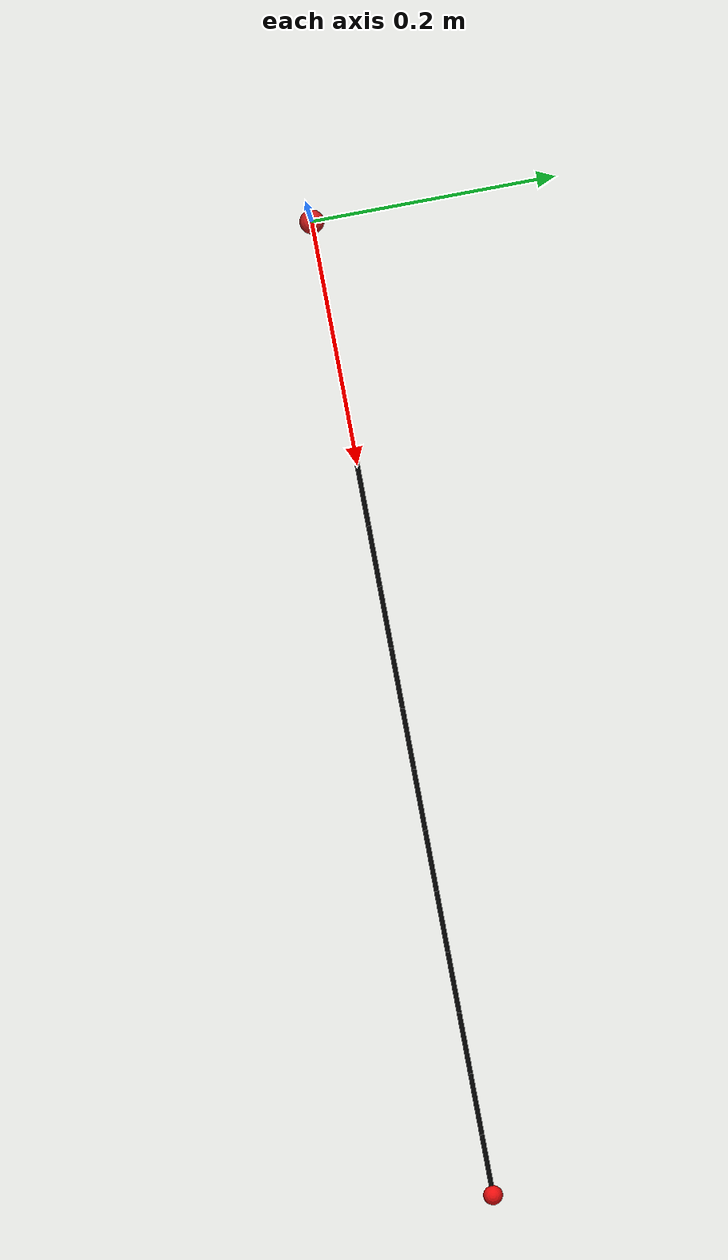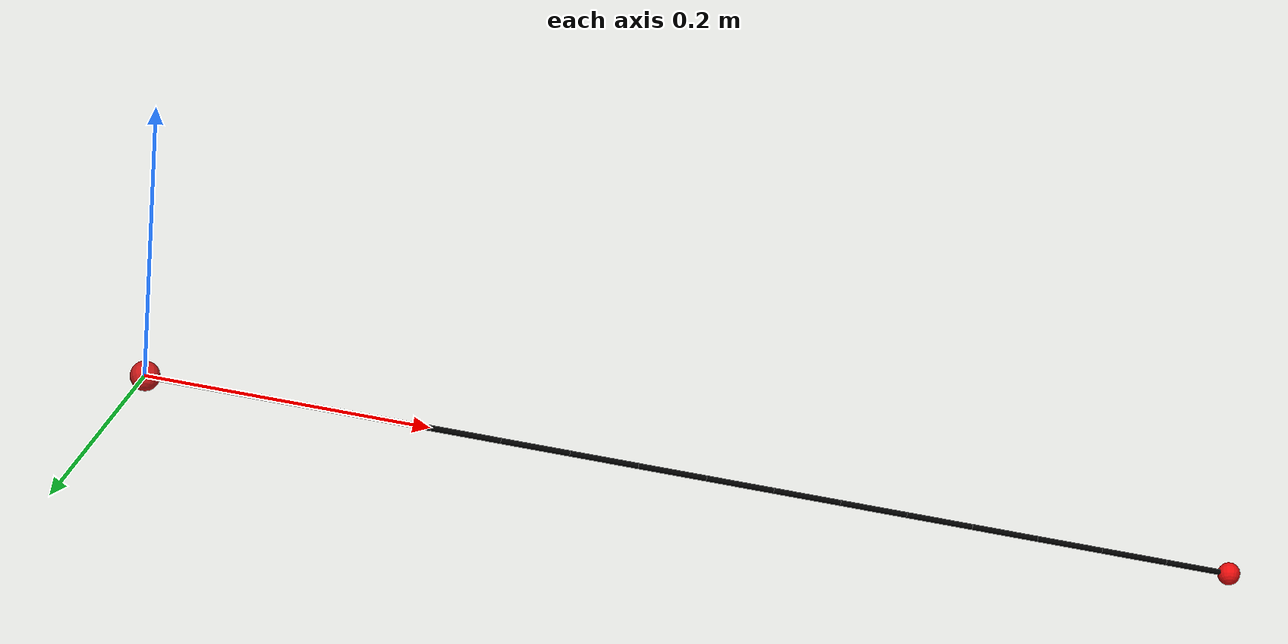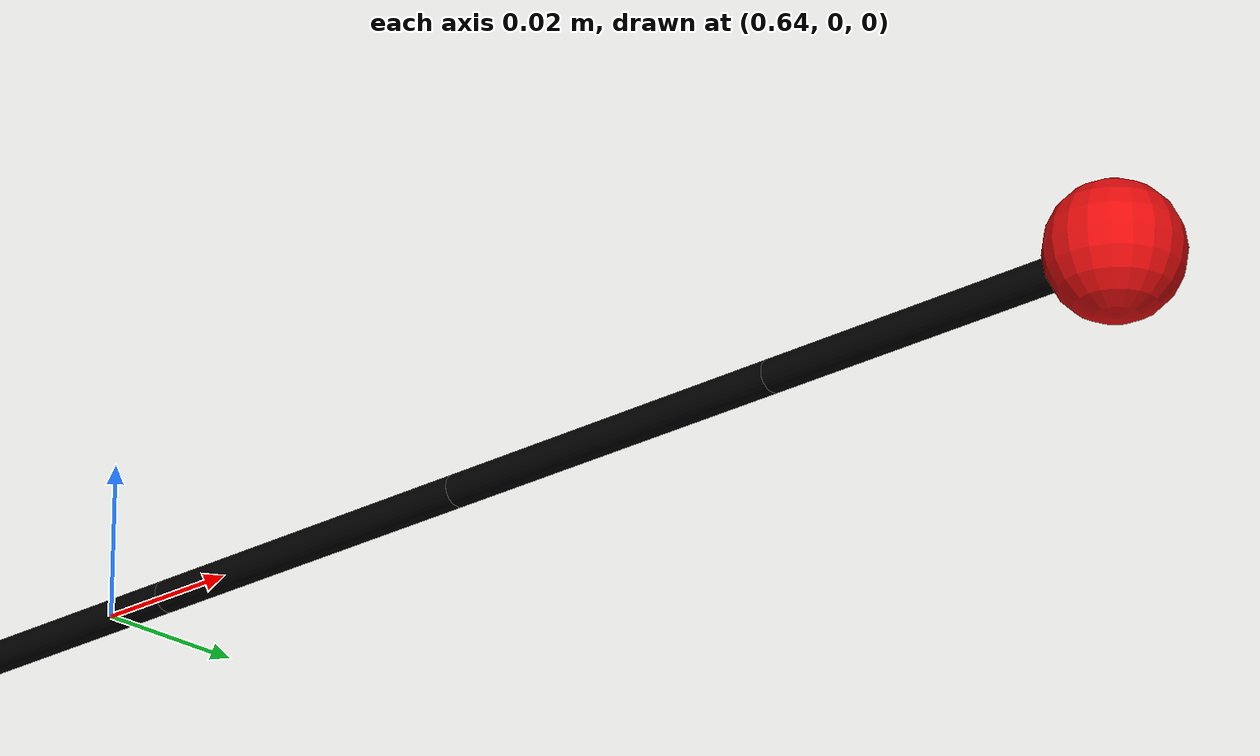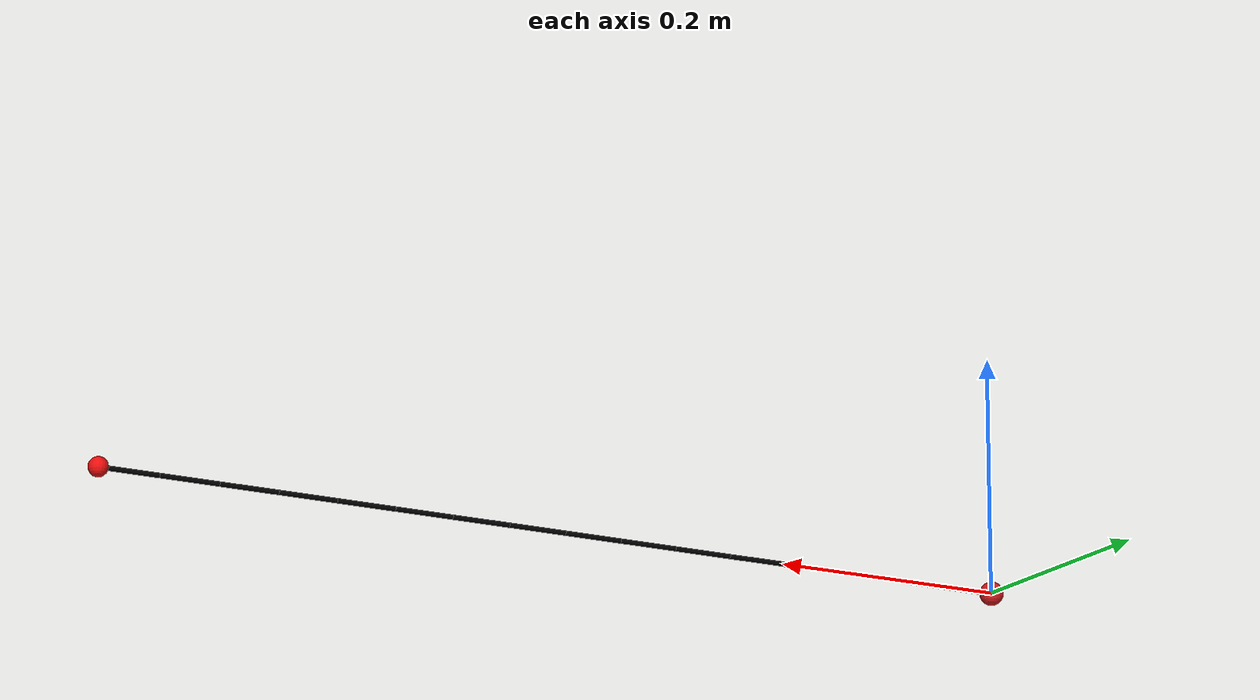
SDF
<?xml version="1.0" ?>
<sdf version="1.8">
  <model name="cabo_flexivel">
    <link name="raiz_cabo">
      <inertial>
        <mass>0.0005</mass>
        <inertia>
          <ixx>8e-7</ixx><ixy>0</ixy><ixz>0</ixz>
          <iyy>8e-7</iyy><iyz>0</iyz><izz>8e-7</izz>
        </inertia>
      </inertial>
      <collision name="col_raiz"><geometry><sphere><radius>0.01</radius></sphere></geometry></collision>
      <visual name="vis_raiz"><geometry><sphere><radius>0.01</radius></sphere></geometry><material><ambient>0.8 0.1 0.1 1</ambient><diffuse>0.8 0.1 0.1 1</diffuse></material></visual>
    </link>

    <joint name="joint_1_y" type="revolute">
      <pose relative_to="raiz_cabo">0.0 0 0 0 0 0</pose>
      <parent>raiz_cabo</parent>
      <child>dummy_1</child>
      <axis>
        <xyz>0 1 0</xyz>
        <limit><lower>-0.7</lower><upper>0.7</upper><effort>5</effort><velocity>10</velocity></limit>
        <dynamics>
          <damping>0.08</damping>
          <friction>0.002</friction>
          <spring_reference>0</spring_reference>
          <spring_stiffness>0.02</spring_stiffness>
        </dynamics>
      </axis>
        <sensor name="sensor_tensao_carretel" type="force_torque">
          <always_on>true</always_on>
          <update_rate>50</update_rate>
          <topic>/cabo/tensao_carretel</topic>
        </sensor>
    </joint>
    <link name="dummy_1">
      <pose relative_to="joint_1_y">0 0 0 0 0 0</pose>
      <inertial><mass>0.0001</mass><inertia><ixx>1e-7</ixx><ixy>0</ixy><ixz>0</ixz><iyy>1e-7</iyy><iyz>0</iyz><izz>1e-7</izz></inertia></inertial>
    </link>
    <joint name="joint_1_z" type="revolute">
      <pose relative_to="dummy_1">0 0 0 0 0 0</pose>
      <parent>dummy_1</parent>
      <child>segment_1</child>
      <axis>
        <xyz>0 0 1</xyz>
        <limit><lower>-0.7</lower><upper>0.7</upper><effort>5</effort><velocity>10</velocity></limit>
        <dynamics>
          <damping>0.08</damping>
          <friction>0.002</friction>
          <spring_reference>0</spring_reference>
          <spring_stiffness>0.02</spring_stiffness>
        </dynamics>
      </axis>
    </joint>
    <link name="segment_1">
      <pose relative_to="joint_1_z">0 0 0 0 0 0</pose>
      <visual name="visual">
        <pose>0.025 0 0 0 1.5708 0</pose>
        <geometry><cylinder><radius>0.002</radius><length>0.05</length></cylinder></geometry>
        <material><ambient>0 0 0 1</ambient><diffuse>0 0 0 1</diffuse></material>
      </visual>
      <collision name="collision">
        <pose>0.025 0 0 0 1.5708 0</pose>
        <geometry><cylinder><radius>0.002</radius><length>0.045000000000000005</length></cylinder></geometry>
      </collision>
      <inertial>
        <pose>0.025 0 0 0 0 0</pose>
        <mass>0.007375</mass>
        <inertia>
          <ixx>1.4749999999999998e-08</ixx><ixy>0</ixy><ixz>0</ixz>
          <iyy>1.5438333333333336e-06</iyy><iyz>0</iyz><izz>1.5438333333333336e-06</izz>
        </inertia>
      </inertial>
    </link>

    <joint name="joint_2_y" type="revolute">
      <pose relative_to="segment_1">0.05 0 0 0 0 0</pose>
      <parent>segment_1</parent>
      <child>dummy_2</child>
      <axis>
        <xyz>0 1 0</xyz>
        <limit><lower>-0.7</lower><upper>0.7</upper><effort>5</effort><velocity>10</velocity></limit>
        <dynamics>
          <damping>0.08</damping>
          <friction>0.002</friction>
          <spring_reference>0</spring_reference>
          <spring_stiffness>0.02</spring_stiffness>
        </dynamics>
      </axis>
    </joint>
    <link name="dummy_2">
      <pose relative_to="joint_2_y">0 0 0 0 0 0</pose>
      <inertial><mass>0.0001</mass><inertia><ixx>1e-7</ixx><ixy>0</ixy><ixz>0</ixz><iyy>1e-7</iyy><iyz>0</iyz><izz>1e-7</izz></inertia></inertial>
    </link>
    <joint name="joint_2_z" type="revolute">
      <pose relative_to="dummy_2">0 0 0 0 0 0</pose>
      <parent>dummy_2</parent>
      <child>segment_2</child>
      <axis>
        <xyz>0 0 1</xyz>
        <limit><lower>-0.7</lower><upper>0.7</upper><effort>5</effort><velocity>10</velocity></limit>
        <dynamics>
          <damping>0.08</damping>
          <friction>0.002</friction>
          <spring_reference>0</spring_reference>
          <spring_stiffness>0.02</spring_stiffness>
        </dynamics>
      </axis>
    </joint>
    <link name="segment_2">
      <pose relative_to="joint_2_z">0 0 0 0 0 0</pose>
      <visual name="visual">
        <pose>0.025 0 0 0 1.5708 0</pose>
        <geometry><cylinder><radius>0.002</radius><length>0.05</length></cylinder></geometry>
        <material><ambient>0 0 0 1</ambient><diffuse>0 0 0 1</diffuse></material>
      </visual>
      <collision name="collision">
        <pose>0.025 0 0 0 1.5708 0</pose>
        <geometry><cylinder><radius>0.002</radius><length>0.045000000000000005</length></cylinder></geometry>
      </collision>
      <inertial>
        <pose>0.025 0 0 0 0 0</pose>
        <mass>0.007375</mass>
        <inertia>
          <ixx>1.4749999999999998e-08</ixx><ixy>0</ixy><ixz>0</ixz>
          <iyy>1.5438333333333336e-06</iyy><iyz>0</iyz><izz>1.5438333333333336e-06</izz>
        </inertia>
      </inertial>
    </link>

    <joint name="joint_3_y" type="revolute">
      <pose relative_to="segment_2">0.05 0 0 0 0 0</pose>
      <parent>segment_2</parent>
      <child>dummy_3</child>
      <axis>
        <xyz>0 1 0</xyz>
        <limit><lower>-0.7</lower><upper>0.7</upper><effort>5</effort><velocity>10</velocity></limit>
        <dynamics>
          <damping>0.08</damping>
          <friction>0.002</friction>
          <spring_reference>0</spring_reference>
          <spring_stiffness>0.02</spring_stiffness>
        </dynamics>
      </axis>
    </joint>
    <link name="dummy_3">
      <pose relative_to="joint_3_y">0 0 0 0 0 0</pose>
      <inertial><mass>0.0001</mass><inertia><ixx>1e-7</ixx><ixy>0</ixy><ixz>0</ixz><iyy>1e-7</iyy><iyz>0</iyz><izz>1e-7</izz></inertia></inertial>
    </link>
    <joint name="joint_3_z" type="revolute">
      <pose relative_to="dummy_3">0 0 0 0 0 0</pose>
      <parent>dummy_3</parent>
      <child>segment_3</child>
      <axis>
        <xyz>0 0 1</xyz>
        <limit><lower>-0.7</lower><upper>0.7</upper><effort>5</effort><velocity>10</velocity></limit>
        <dynamics>
          <damping>0.08</damping>
          <friction>0.002</friction>
          <spring_reference>0</spring_reference>
          <spring_stiffness>0.02</spring_stiffness>
        </dynamics>
      </axis>
    </joint>
    <link name="segment_3">
      <pose relative_to="joint_3_z">0 0 0 0 0 0</pose>
      <visual name="visual">
        <pose>0.025 0 0 0 1.5708 0</pose>
        <geometry><cylinder><radius>0.002</radius><length>0.05</length></cylinder></geometry>
        <material><ambient>0 0 0 1</ambient><diffuse>0 0 0 1</diffuse></material>
      </visual>
      <collision name="collision">
        <pose>0.025 0 0 0 1.5708 0</pose>
        <geometry><cylinder><radius>0.002</radius><length>0.045000000000000005</length></cylinder></geometry>
      </collision>
      <inertial>
        <pose>0.025 0 0 0 0 0</pose>
        <mass>0.007375</mass>
        <inertia>
          <ixx>1.4749999999999998e-08</ixx><ixy>0</ixy><ixz>0</ixz>
          <iyy>1.5438333333333336e-06</iyy><iyz>0</iyz><izz>1.5438333333333336e-06</izz>
        </inertia>
      </inertial>
    </link>

    <joint name="joint_4_y" type="revolute">
      <pose relative_to="segment_3">0.05 0 0 0 0 0</pose>
      <parent>segment_3</parent>
      <child>dummy_4</child>
      <axis>
        <xyz>0 1 0</xyz>
        <limit><lower>-0.7</lower><upper>0.7</upper><effort>5</effort><velocity>10</velocity></limit>
        <dynamics>
          <damping>0.08</damping>
          <friction>0.002</friction>
          <spring_reference>0</spring_reference>
          <spring_stiffness>0.02</spring_stiffness>
        </dynamics>
      </axis>
    </joint>
    <link name="dummy_4">
      <pose relative_to="joint_4_y">0 0 0 0 0 0</pose>
      <inertial><mass>0.0001</mass><inertia><ixx>1e-7</ixx><ixy>0</ixy><ixz>0</ixz><iyy>1e-7</iyy><iyz>0</iyz><izz>1e-7</izz></inertia></inertial>
    </link>
    <joint name="joint_4_z" type="revolute">
      <pose relative_to="dummy_4">0 0 0 0 0 0</pose>
      <parent>dummy_4</parent>
      <child>segment_4</child>
      <axis>
        <xyz>0 0 1</xyz>
        <limit><lower>-0.7</lower><upper>0.7</upper><effort>5</effort><velocity>10</velocity></limit>
        <dynamics>
          <damping>0.08</damping>
          <friction>0.002</friction>
          <spring_reference>0</spring_reference>
          <spring_stiffness>0.02</spring_stiffness>
        </dynamics>
      </axis>
    </joint>
    <link name="segment_4">
      <pose relative_to="joint_4_z">0 0 0 0 0 0</pose>
      <visual name="visual">
        <pose>0.025 0 0 0 1.5708 0</pose>
        <geometry><cylinder><radius>0.002</radius><length>0.05</length></cylinder></geometry>
        <material><ambient>0 0 0 1</ambient><diffuse>0 0 0 1</diffuse></material>
      </visual>
      <collision name="collision">
        <pose>0.025 0 0 0 1.5708 0</pose>
        <geometry><cylinder><radius>0.002</radius><length>0.045000000000000005</length></cylinder></geometry>
      </collision>
      <inertial>
        <pose>0.025 0 0 0 0 0</pose>
        <mass>0.007375</mass>
        <inertia>
          <ixx>1.4749999999999998e-08</ixx><ixy>0</ixy><ixz>0</ixz>
          <iyy>1.5438333333333336e-06</iyy><iyz>0</iyz><izz>1.5438333333333336e-06</izz>
        </inertia>
      </inertial>
    </link>

    <joint name="joint_5_y" type="revolute">
      <pose relative_to="segment_4">0.05 0 0 0 0 0</pose>
      <parent>segment_4</parent>
      <child>dummy_5</child>
      <axis>
        <xyz>0 1 0</xyz>
        <limit><lower>-0.7</lower><upper>0.7</upper><effort>5</effort><velocity>10</velocity></limit>
        <dynamics>
          <damping>0.08</damping>
          <friction>0.002</friction>
          <spring_reference>0</spring_reference>
          <spring_stiffness>0.02</spring_stiffness>
        </dynamics>
      </axis>
    </joint>
    <link name="dummy_5">
      <pose relative_to="joint_5_y">0 0 0 0 0 0</pose>
      <inertial><mass>0.0001</mass><inertia><ixx>1e-7</ixx><ixy>0</ixy><ixz>0</ixz><iyy>1e-7</iyy><iyz>0</iyz><izz>1e-7</izz></inertia></inertial>
    </link>
    <joint name="joint_5_z" type="revolute">
      <pose relative_to="dummy_5">0 0 0 0 0 0</pose>
      <parent>dummy_5</parent>
      <child>segment_5</child>
      <axis>
        <xyz>0 0 1</xyz>
        <limit><lower>-0.7</lower><upper>0.7</upper><effort>5</effort><velocity>10</velocity></limit>
        <dynamics>
          <damping>0.08</damping>
          <friction>0.002</friction>
          <spring_reference>0</spring_reference>
          <spring_stiffness>0.02</spring_stiffness>
        </dynamics>
      </axis>
    </joint>
    <link name="segment_5">
      <pose relative_to="joint_5_z">0 0 0 0 0 0</pose>
      <visual name="visual">
        <pose>0.025 0 0 0 1.5708 0</pose>
        <geometry><cylinder><radius>0.002</radius><length>0.05</length></cylinder></geometry>
        <material><ambient>0 0 0 1</ambient><diffuse>0 0 0 1</diffuse></material>
      </visual>
      <collision name="collision">
        <pose>0.025 0 0 0 1.5708 0</pose>
        <geometry><cylinder><radius>0.002</radius><length>0.045000000000000005</length></cylinder></geometry>
      </collision>
      <inertial>
        <pose>0.025 0 0 0 0 0</pose>
        <mass>0.007375</mass>
        <inertia>
          <ixx>1.4749999999999998e-08</ixx><ixy>0</ixy><ixz>0</ixz>
          <iyy>1.5438333333333336e-06</iyy><iyz>0</iyz><izz>1.5438333333333336e-06</izz>
        </inertia>
      </inertial>
    </link>

    <joint name="joint_6_y" type="revolute">
      <pose relative_to="segment_5">0.05 0 0 0 0 0</pose>
      <parent>segment_5</parent>
      <child>dummy_6</child>
      <axis>
        <xyz>0 1 0</xyz>
        <limit><lower>-0.7</lower><upper>0.7</upper><effort>5</effort><velocity>10</velocity></limit>
        <dynamics>
          <damping>0.08</damping>
          <friction>0.002</friction>
          <spring_reference>0</spring_reference>
          <spring_stiffness>0.02</spring_stiffness>
        </dynamics>
      </axis>
    </joint>
    <link name="dummy_6">
      <pose relative_to="joint_6_y">0 0 0 0 0 0</pose>
      <inertial><mass>0.0001</mass><inertia><ixx>1e-7</ixx><ixy>0</ixy><ixz>0</ixz><iyy>1e-7</iyy><iyz>0</iyz><izz>1e-7</izz></inertia></inertial>
    </link>
    <joint name="joint_6_z" type="revolute">
      <pose relative_to="dummy_6">0 0 0 0 0 0</pose>
      <parent>dummy_6</parent>
      <child>segment_6</child>
      <axis>
        <xyz>0 0 1</xyz>
        <limit><lower>-0.7</lower><upper>0.7</upper><effort>5</effort><velocity>10</velocity></limit>
        <dynamics>
          <damping>0.08</damping>
          <friction>0.002</friction>
          <spring_reference>0</spring_reference>
          <spring_stiffness>0.02</spring_stiffness>
        </dynamics>
      </axis>
    </joint>
    <link name="segment_6">
      <pose relative_to="joint_6_z">0 0 0 0 0 0</pose>
      <visual name="visual">
        <pose>0.025 0 0 0 1.5708 0</pose>
        <geometry><cylinder><radius>0.002</radius><length>0.05</length></cylinder></geometry>
        <material><ambient>0 0 0 1</ambient><diffuse>0 0 0 1</diffuse></material>
      </visual>
      <collision name="collision">
        <pose>0.025 0 0 0 1.5708 0</pose>
        <geometry><cylinder><radius>0.002</radius><length>0.045000000000000005</length></cylinder></geometry>
      </collision>
      <inertial>
        <pose>0.025 0 0 0 0 0</pose>
        <mass>0.007375</mass>
        <inertia>
          <ixx>1.4749999999999998e-08</ixx><ixy>0</ixy><ixz>0</ixz>
          <iyy>1.5438333333333336e-06</iyy><iyz>0</iyz><izz>1.5438333333333336e-06</izz>
        </inertia>
      </inertial>
    </link>

    <joint name="joint_7_y" type="revolute">
      <pose relative_to="segment_6">0.05 0 0 0 0 0</pose>
      <parent>segment_6</parent>
      <child>dummy_7</child>
      <axis>
        <xyz>0 1 0</xyz>
        <limit><lower>-0.7</lower><upper>0.7</upper><effort>5</effort><velocity>10</velocity></limit>
        <dynamics>
          <damping>0.08</damping>
          <friction>0.002</friction>
          <spring_reference>0</spring_reference>
          <spring_stiffness>0.02</spring_stiffness>
        </dynamics>
      </axis>
    </joint>
    <link name="dummy_7">
      <pose relative_to="joint_7_y">0 0 0 0 0 0</pose>
      <inertial><mass>0.0001</mass><inertia><ixx>1e-7</ixx><ixy>0</ixy><ixz>0</ixz><iyy>1e-7</iyy><iyz>0</iyz><izz>1e-7</izz></inertia></inertial>
    </link>
    <joint name="joint_7_z" type="revolute">
      <pose relative_to="dummy_7">0 0 0 0 0 0</pose>
      <parent>dummy_7</parent>
      <child>segment_7</child>
      <axis>
        <xyz>0 0 1</xyz>
        <limit><lower>-0.7</lower><upper>0.7</upper><effort>5</effort><velocity>10</velocity></limit>
        <dynamics>
          <damping>0.08</damping>
          <friction>0.002</friction>
          <spring_reference>0</spring_reference>
          <spring_stiffness>0.02</spring_stiffness>
        </dynamics>
      </axis>
    </joint>
    <link name="segment_7">
      <pose relative_to="joint_7_z">0 0 0 0 0 0</pose>
      <visual name="visual">
        <pose>0.025 0 0 0 1.5708 0</pose>
        <geometry><cylinder><radius>0.002</radius><length>0.05</length></cylinder></geometry>
        <material><ambient>0 0 0 1</ambient><diffuse>0 0 0 1</diffuse></material>
      </visual>
      <collision name="collision">
        <pose>0.025 0 0 0 1.5708 0</pose>
        <geometry><cylinder><radius>0.002</radius><length>0.045000000000000005</length></cylinder></geometry>
      </collision>
      <inertial>
        <pose>0.025 0 0 0 0 0</pose>
        <mass>0.007375</mass>
        <inertia>
          <ixx>1.4749999999999998e-08</ixx><ixy>0</ixy><ixz>0</ixz>
          <iyy>1.5438333333333336e-06</iyy><iyz>0</iyz><izz>1.5438333333333336e-06</izz>
        </inertia>
      </inertial>
    </link>

    <joint name="joint_8_y" type="revolute">
      <pose relative_to="segment_7">0.05 0 0 0 0 0</pose>
      <parent>segment_7</parent>
      <child>dummy_8</child>
      <axis>
        <xyz>0 1 0</xyz>
        <limit><lower>-0.7</lower><upper>0.7</upper><effort>5</effort><velocity>10</velocity></limit>
        <dynamics>
          <damping>0.08</damping>
          <friction>0.002</friction>
          <spring_reference>0</spring_reference>
          <spring_stiffness>0.02</spring_stiffness>
        </dynamics>
      </axis>
    </joint>
    <link name="dummy_8">
      <pose relative_to="joint_8_y">0 0 0 0 0 0</pose>
      <inertial><mass>0.0001</mass><inertia><ixx>1e-7</ixx><ixy>0</ixy><ixz>0</ixz><iyy>1e-7</iyy><iyz>0</iyz><izz>1e-7</izz></inertia></inertial>
    </link>
    <joint name="joint_8_z" type="revolute">
      <pose relative_to="dummy_8">0 0 0 0 0 0</pose>
      <parent>dummy_8</parent>
      <child>segment_8</child>
      <axis>
        <xyz>0 0 1</xyz>
        <limit><lower>-0.7</lower><upper>0.7</upper><effort>5</effort><velocity>10</velocity></limit>
        <dynamics>
          <damping>0.08</damping>
          <friction>0.002</friction>
          <spring_reference>0</spring_reference>
          <spring_stiffness>0.02</spring_stiffness>
        </dynamics>
      </axis>
    </joint>
    <link name="segment_8">
      <pose relative_to="joint_8_z">0 0 0 0 0 0</pose>
      <visual name="visual">
        <pose>0.025 0 0 0 1.5708 0</pose>
        <geometry><cylinder><radius>0.002</radius><length>0.05</length></cylinder></geometry>
        <material><ambient>0 0 0 1</ambient><diffuse>0 0 0 1</diffuse></material>
      </visual>
      <collision name="collision">
        <pose>0.025 0 0 0 1.5708 0</pose>
        <geometry><cylinder><radius>0.002</radius><length>0.045000000000000005</length></cylinder></geometry>
      </collision>
      <inertial>
        <pose>0.025 0 0 0 0 0</pose>
        <mass>0.007375</mass>
        <inertia>
          <ixx>1.4749999999999998e-08</ixx><ixy>0</ixy><ixz>0</ixz>
          <iyy>1.5438333333333336e-06</iyy><iyz>0</iyz><izz>1.5438333333333336e-06</izz>
        </inertia>
      </inertial>
    </link>

    <joint name="joint_9_y" type="revolute">
      <pose relative_to="segment_8">0.05 0 0 0 0 0</pose>
      <parent>segment_8</parent>
      <child>dummy_9</child>
      <axis>
        <xyz>0 1 0</xyz>
        <limit><lower>-0.7</lower><upper>0.7</upper><effort>5</effort><velocity>10</velocity></limit>
        <dynamics>
          <damping>0.08</damping>
          <friction>0.002</friction>
          <spring_reference>0</spring_reference>
          <spring_stiffness>0.02</spring_stiffness>
        </dynamics>
      </axis>
    </joint>
    <link name="dummy_9">
      <pose relative_to="joint_9_y">0 0 0 0 0 0</pose>
      <inertial><mass>0.0001</mass><inertia><ixx>1e-7</ixx><ixy>0</ixy><ixz>0</ixz><iyy>1e-7</iyy><iyz>0</iyz><izz>1e-7</izz></inertia></inertial>
    </link>
    <joint name="joint_9_z" type="revolute">
      <pose relative_to="dummy_9">0 0 0 0 0 0</pose>
      <parent>dummy_9</parent>
      <child>segment_9</child>
      <axis>
        <xyz>0 0 1</xyz>
        <limit><lower>-0.7</lower><upper>0.7</upper><effort>5</effort><velocity>10</velocity></limit>
        <dynamics>
          <damping>0.08</damping>
          <friction>0.002</friction>
          <spring_reference>0</spring_reference>
          <spring_stiffness>0.02</spring_stiffness>
        </dynamics>
      </axis>
    </joint>
    <link name="segment_9">
      <pose relative_to="joint_9_z">0 0 0 0 0 0</pose>
      <visual name="visual">
        <pose>0.025 0 0 0 1.5708 0</pose>
        <geometry><cylinder><radius>0.002</radius><length>0.05</length></cylinder></geometry>
        <material><ambient>0 0 0 1</ambient><diffuse>0 0 0 1</diffuse></material>
      </visual>
      <collision name="collision">
        <pose>0.025 0 0 0 1.5708 0</pose>
        <geometry><cylinder><radius>0.002</radius><length>0.045000000000000005</length></cylinder></geometry>
      </collision>
      <inertial>
        <pose>0.025 0 0 0 0 0</pose>
        <mass>0.007375</mass>
        <inertia>
          <ixx>1.4749999999999998e-08</ixx><ixy>0</ixy><ixz>0</ixz>
          <iyy>1.5438333333333336e-06</iyy><iyz>0</iyz><izz>1.5438333333333336e-06</izz>
        </inertia>
      </inertial>
    </link>

    <joint name="joint_10_y" type="revolute">
      <pose relative_to="segment_9">0.05 0 0 0 0 0</pose>
      <parent>segment_9</parent>
      <child>dummy_10</child>
      <axis>
        <xyz>0 1 0</xyz>
        <limit><lower>-0.7</lower><upper>0.7</upper><effort>5</effort><velocity>10</velocity></limit>
        <dynamics>
          <damping>0.08</damping>
          <friction>0.002</friction>
          <spring_reference>0</spring_reference>
          <spring_stiffness>0.02</spring_stiffness>
        </dynamics>
      </axis>
    </joint>
    <link name="dummy_10">
      <pose relative_to="joint_10_y">0 0 0 0 0 0</pose>
      <inertial><mass>0.0001</mass><inertia><ixx>1e-7</ixx><ixy>0</ixy><ixz>0</ixz><iyy>1e-7</iyy><iyz>0</iyz><izz>1e-7</izz></inertia></inertial>
    </link>
    <joint name="joint_10_z" type="revolute">
      <pose relative_to="dummy_10">0 0 0 0 0 0</pose>
      <parent>dummy_10</parent>
      <child>segment_10</child>
      <axis>
        <xyz>0 0 1</xyz>
        <limit><lower>-0.7</lower><upper>0.7</upper><effort>5</effort><velocity>10</velocity></limit>
        <dynamics>
          <damping>0.08</damping>
          <friction>0.002</friction>
          <spring_reference>0</spring_reference>
          <spring_stiffness>0.02</spring_stiffness>
        </dynamics>
      </axis>
    </joint>
    <link name="segment_10">
      <pose relative_to="joint_10_z">0 0 0 0 0 0</pose>
      <visual name="visual">
        <pose>0.025 0 0 0 1.5708 0</pose>
        <geometry><cylinder><radius>0.002</radius><length>0.05</length></cylinder></geometry>
        <material><ambient>0 0 0 1</ambient><diffuse>0 0 0 1</diffuse></material>
      </visual>
      <collision name="collision">
        <pose>0.025 0 0 0 1.5708 0</pose>
        <geometry><cylinder><radius>0.002</radius><length>0.045000000000000005</length></cylinder></geometry>
      </collision>
      <inertial>
        <pose>0.025 0 0 0 0 0</pose>
        <mass>0.007375</mass>
        <inertia>
          <ixx>1.4749999999999998e-08</ixx><ixy>0</ixy><ixz>0</ixz>
          <iyy>1.5438333333333336e-06</iyy><iyz>0</iyz><izz>1.5438333333333336e-06</izz>
        </inertia>
      </inertial>
    </link>

    <joint name="joint_11_y" type="revolute">
      <pose relative_to="segment_10">0.05 0 0 0 0 0</pose>
      <parent>segment_10</parent>
      <child>dummy_11</child>
      <axis>
        <xyz>0 1 0</xyz>
        <limit><lower>-0.7</lower><upper>0.7</upper><effort>5</effort><velocity>10</velocity></limit>
        <dynamics>
          <damping>0.08</damping>
          <friction>0.002</friction>
          <spring_reference>0</spring_reference>
          <spring_stiffness>0.02</spring_stiffness>
        </dynamics>
      </axis>
    </joint>
    <link name="dummy_11">
      <pose relative_to="joint_11_y">0 0 0 0 0 0</pose>
      <inertial><mass>0.0001</mass><inertia><ixx>1e-7</ixx><ixy>0</ixy><ixz>0</ixz><iyy>1e-7</iyy><iyz>0</iyz><izz>1e-7</izz></inertia></inertial>
    </link>
    <joint name="joint_11_z" type="revolute">
      <pose relative_to="dummy_11">0 0 0 0 0 0</pose>
      <parent>dummy_11</parent>
      <child>segment_11</child>
      <axis>
        <xyz>0 0 1</xyz>
        <limit><lower>-0.7</lower><upper>0.7</upper><effort>5</effort><velocity>10</velocity></limit>
        <dynamics>
          <damping>0.08</damping>
          <friction>0.002</friction>
          <spring_reference>0</spring_reference>
          <spring_stiffness>0.02</spring_stiffness>
        </dynamics>
      </axis>
    </joint>
    <link name="segment_11">
      <pose relative_to="joint_11_z">0 0 0 0 0 0</pose>
      <visual name="visual">
        <pose>0.025 0 0 0 1.5708 0</pose>
        <geometry><cylinder><radius>0.002</radius><length>0.05</length></cylinder></geometry>
        <material><ambient>0 0 0 1</ambient><diffuse>0 0 0 1</diffuse></material>
      </visual>
      <collision name="collision">
        <pose>0.025 0 0 0 1.5708 0</pose>
        <geometry><cylinder><radius>0.002</radius><length>0.045000000000000005</length></cylinder></geometry>
      </collision>
      <inertial>
        <pose>0.025 0 0 0 0 0</pose>
        <mass>0.007375</mass>
        <inertia>
          <ixx>1.4749999999999998e-08</ixx><ixy>0</ixy><ixz>0</ixz>
          <iyy>1.5438333333333336e-06</iyy><iyz>0</iyz><izz>1.5438333333333336e-06</izz>
        </inertia>
      </inertial>
    </link>

    <joint name="joint_12_y" type="revolute">
      <pose relative_to="segment_11">0.05 0 0 0 0 0</pose>
      <parent>segment_11</parent>
      <child>dummy_12</child>
      <axis>
        <xyz>0 1 0</xyz>
        <limit><lower>-0.7</lower><upper>0.7</upper><effort>5</effort><velocity>10</velocity></limit>
        <dynamics>
          <damping>0.08</damping>
          <friction>0.002</friction>
          <spring_reference>0</spring_reference>
          <spring_stiffness>0.02</spring_stiffness>
        </dynamics>
      </axis>
    </joint>
    <link name="dummy_12">
      <pose relative_to="joint_12_y">0 0 0 0 0 0</pose>
      <inertial><mass>0.0001</mass><inertia><ixx>1e-7</ixx><ixy>0</ixy><ixz>0</ixz><iyy>1e-7</iyy><iyz>0</iyz><izz>1e-7</izz></inertia></inertial>
    </link>
    <joint name="joint_12_z" type="revolute">
      <pose relative_to="dummy_12">0 0 0 0 0 0</pose>
      <parent>dummy_12</parent>
      <child>segment_12</child>
      <axis>
        <xyz>0 0 1</xyz>
        <limit><lower>-0.7</lower><upper>0.7</upper><effort>5</effort><velocity>10</velocity></limit>
        <dynamics>
          <damping>0.08</damping>
          <friction>0.002</friction>
          <spring_reference>0</spring_reference>
          <spring_stiffness>0.02</spring_stiffness>
        </dynamics>
      </axis>
    </joint>
    <link name="segment_12">
      <pose relative_to="joint_12_z">0 0 0 0 0 0</pose>
      <visual name="visual">
        <pose>0.025 0 0 0 1.5708 0</pose>
        <geometry><cylinder><radius>0.002</radius><length>0.05</length></cylinder></geometry>
        <material><ambient>0 0 0 1</ambient><diffuse>0 0 0 1</diffuse></material>
      </visual>
      <collision name="collision">
        <pose>0.025 0 0 0 1.5708 0</pose>
        <geometry><cylinder><radius>0.002</radius><length>0.045000000000000005</length></cylinder></geometry>
      </collision>
      <inertial>
        <pose>0.025 0 0 0 0 0</pose>
        <mass>0.007375</mass>
        <inertia>
          <ixx>1.4749999999999998e-08</ixx><ixy>0</ixy><ixz>0</ixz>
          <iyy>1.5438333333333336e-06</iyy><iyz>0</iyz><izz>1.5438333333333336e-06</izz>
        </inertia>
      </inertial>
    </link>

    <joint name="joint_13_y" type="revolute">
      <pose relative_to="segment_12">0.05 0 0 0 0 0</pose>
      <parent>segment_12</parent>
      <child>dummy_13</child>
      <axis>
        <xyz>0 1 0</xyz>
        <limit><lower>-0.7</lower><upper>0.7</upper><effort>5</effort><velocity>10</velocity></limit>
        <dynamics>
          <damping>0.08</damping>
          <friction>0.002</friction>
          <spring_reference>0</spring_reference>
          <spring_stiffness>0.02</spring_stiffness>
        </dynamics>
      </axis>
    </joint>
    <link name="dummy_13">
      <pose relative_to="joint_13_y">0 0 0 0 0 0</pose>
      <inertial><mass>0.0001</mass><inertia><ixx>1e-7</ixx><ixy>0</ixy><ixz>0</ixz><iyy>1e-7</iyy><iyz>0</iyz><izz>1e-7</izz></inertia></inertial>
    </link>
    <joint name="joint_13_z" type="revolute">
      <pose relative_to="dummy_13">0 0 0 0 0 0</pose>
      <parent>dummy_13</parent>
      <child>segment_13</child>
      <axis>
        <xyz>0 0 1</xyz>
        <limit><lower>-0.7</lower><upper>0.7</upper><effort>5</effort><velocity>10</velocity></limit>
        <dynamics>
          <damping>0.08</damping>
          <friction>0.002</friction>
          <spring_reference>0</spring_reference>
          <spring_stiffness>0.02</spring_stiffness>
        </dynamics>
      </axis>
    </joint>
    <link name="segment_13">
      <pose relative_to="joint_13_z">0 0 0 0 0 0</pose>
      <visual name="visual">
        <pose>0.025 0 0 0 1.5708 0</pose>
        <geometry><cylinder><radius>0.002</radius><length>0.05</length></cylinder></geometry>
        <material><ambient>0 0 0 1</ambient><diffuse>0 0 0 1</diffuse></material>
      </visual>
      <collision name="collision">
        <pose>0.025 0 0 0 1.5708 0</pose>
        <geometry><cylinder><radius>0.002</radius><length>0.045000000000000005</length></cylinder></geometry>
      </collision>
      <inertial>
        <pose>0.025 0 0 0 0 0</pose>
        <mass>0.007375</mass>
        <inertia>
          <ixx>1.4749999999999998e-08</ixx><ixy>0</ixy><ixz>0</ixz>
          <iyy>1.5438333333333336e-06</iyy><iyz>0</iyz><izz>1.5438333333333336e-06</izz>
        </inertia>
      </inertial>
    </link>

    <joint name="joint_14_y" type="revolute">
      <pose relative_to="segment_13">0.05 0 0 0 0 0</pose>
      <parent>segment_13</parent>
      <child>dummy_14</child>
      <axis>
        <xyz>0 1 0</xyz>
        <limit><lower>-0.7</lower><upper>0.7</upper><effort>5</effort><velocity>10</velocity></limit>
        <dynamics>
          <damping>0.08</damping>
          <friction>0.002</friction>
          <spring_reference>0</spring_reference>
          <spring_stiffness>0.02</spring_stiffness>
        </dynamics>
      </axis>
    </joint>
    <link name="dummy_14">
      <pose relative_to="joint_14_y">0 0 0 0 0 0</pose>
      <inertial><mass>0.0001</mass><inertia><ixx>1e-7</ixx><ixy>0</ixy><ixz>0</ixz><iyy>1e-7</iyy><iyz>0</iyz><izz>1e-7</izz></inertia></inertial>
    </link>
    <joint name="joint_14_z" type="revolute">
      <pose relative_to="dummy_14">0 0 0 0 0 0</pose>
      <parent>dummy_14</parent>
      <child>segment_14</child>
      <axis>
        <xyz>0 0 1</xyz>
        <limit><lower>-0.7</lower><upper>0.7</upper><effort>5</effort><velocity>10</velocity></limit>
        <dynamics>
          <damping>0.08</damping>
          <friction>0.002</friction>
          <spring_reference>0</spring_reference>
          <spring_stiffness>0.02</spring_stiffness>
        </dynamics>
      </axis>
    </joint>
    <link name="segment_14">
      <pose relative_to="joint_14_z">0 0 0 0 0 0</pose>
      <visual name="visual">
        <pose>0.025 0 0 0 1.5708 0</pose>
        <geometry><cylinder><radius>0.002</radius><length>0.05</length></cylinder></geometry>
        <material><ambient>0 0 0 1</ambient><diffuse>0 0 0 1</diffuse></material>
      </visual>
      <collision name="collision">
        <pose>0.025 0 0 0 1.5708 0</pose>
        <geometry><cylinder><radius>0.002</radius><length>0.045000000000000005</length></cylinder></geometry>
      </collision>
      <inertial>
        <pose>0.025 0 0 0 0 0</pose>
        <mass>0.007375</mass>
        <inertia>
          <ixx>1.4749999999999998e-08</ixx><ixy>0</ixy><ixz>0</ixz>
          <iyy>1.5438333333333336e-06</iyy><iyz>0</iyz><izz>1.5438333333333336e-06</izz>
        </inertia>
      </inertial>
    </link>

    <joint name="joint_15_y" type="revolute">
      <pose relative_to="segment_14">0.05 0 0 0 0 0</pose>
      <parent>segment_14</parent>
      <child>dummy_15</child>
      <axis>
        <xyz>0 1 0</xyz>
        <limit><lower>-0.7</lower><upper>0.7</upper><effort>5</effort><velocity>10</velocity></limit>
        <dynamics>
          <damping>0.08</damping>
          <friction>0.002</friction>
          <spring_reference>0</spring_reference>
          <spring_stiffness>0.02</spring_stiffness>
        </dynamics>
      </axis>
    </joint>
    <link name="dummy_15">
      <pose relative_to="joint_15_y">0 0 0 0 0 0</pose>
      <inertial><mass>0.0001</mass><inertia><ixx>1e-7</ixx><ixy>0</ixy><ixz>0</ixz><iyy>1e-7</iyy><iyz>0</iyz><izz>1e-7</izz></inertia></inertial>
    </link>
    <joint name="joint_15_z" type="revolute">
      <pose relative_to="dummy_15">0 0 0 0 0 0</pose>
      <parent>dummy_15</parent>
      <child>segment_15</child>
      <axis>
        <xyz>0 0 1</xyz>
        <limit><lower>-0.7</lower><upper>0.7</upper><effort>5</effort><velocity>10</velocity></limit>
        <dynamics>
          <damping>0.08</damping>
          <friction>0.002</friction>
          <spring_reference>0</spring_reference>
          <spring_stiffness>0.02</spring_stiffness>
        </dynamics>
      </axis>
    </joint>
    <link name="segment_15">
      <pose relative_to="joint_15_z">0 0 0 0 0 0</pose>
      <visual name="visual">
        <pose>0.025 0 0 0 1.5708 0</pose>
        <geometry><cylinder><radius>0.002</radius><length>0.05</length></cylinder></geometry>
        <material><ambient>0 0 0 1</ambient><diffuse>0 0 0 1</diffuse></material>
      </visual>
      <collision name="collision">
        <pose>0.025 0 0 0 1.5708 0</pose>
        <geometry><cylinder><radius>0.002</radius><length>0.045000000000000005</length></cylinder></geometry>
      </collision>
      <inertial>
        <pose>0.025 0 0 0 0 0</pose>
        <mass>0.007375</mass>
        <inertia>
          <ixx>1.4749999999999998e-08</ixx><ixy>0</ixy><ixz>0</ixz>
          <iyy>1.5438333333333336e-06</iyy><iyz>0</iyz><izz>1.5438333333333336e-06</izz>
        </inertia>
      </inertial>
    </link>

    <joint name="joint_16_y" type="revolute">
      <pose relative_to="segment_15">0.05 0 0 0 0 0</pose>
      <parent>segment_15</parent>
      <child>dummy_16</child>
      <axis>
        <xyz>0 1 0</xyz>
        <limit><lower>-0.7</lower><upper>0.7</upper><effort>5</effort><velocity>10</velocity></limit>
        <dynamics>
          <damping>0.08</damping>
          <friction>0.002</friction>
          <spring_reference>0</spring_reference>
          <spring_stiffness>0.02</spring_stiffness>
        </dynamics>
      </axis>
    </joint>
    <link name="dummy_16">
      <pose relative_to="joint_16_y">0 0 0 0 0 0</pose>
      <inertial><mass>0.0001</mass><inertia><ixx>1e-7</ixx><ixy>0</ixy><ixz>0</ixz><iyy>1e-7</iyy><iyz>0</iyz><izz>1e-7</izz></inertia></inertial>
    </link>
    <joint name="joint_16_z" type="revolute">
      <pose relative_to="dummy_16">0 0 0 0 0 0</pose>
      <parent>dummy_16</parent>
      <child>segment_16</child>
      <axis>
        <xyz>0 0 1</xyz>
        <limit><lower>-0.7</lower><upper>0.7</upper><effort>5</effort><velocity>10</velocity></limit>
        <dynamics>
          <damping>0.08</damping>
          <friction>0.002</friction>
          <spring_reference>0</spring_reference>
          <spring_stiffness>0.02</spring_stiffness>
        </dynamics>
      </axis>
    </joint>
    <link name="segment_16">
      <pose relative_to="joint_16_z">0 0 0 0 0 0</pose>
      <visual name="visual">
        <pose>0.025 0 0 0 1.5708 0</pose>
        <geometry><cylinder><radius>0.002</radius><length>0.05</length></cylinder></geometry>
        <material><ambient>0 0 0 1</ambient><diffuse>0 0 0 1</diffuse></material>
      </visual>
      <collision name="collision">
        <pose>0.025 0 0 0 1.5708 0</pose>
        <geometry><cylinder><radius>0.002</radius><length>0.045000000000000005</length></cylinder></geometry>
      </collision>
      <inertial>
        <pose>0.025 0 0 0 0 0</pose>
        <mass>0.007375</mass>
        <inertia>
          <ixx>1.4749999999999998e-08</ixx><ixy>0</ixy><ixz>0</ixz>
          <iyy>1.5438333333333336e-06</iyy><iyz>0</iyz><izz>1.5438333333333336e-06</izz>
        </inertia>
      </inertial>
    </link>

    <joint name="joint_17_y" type="revolute">
      <pose relative_to="segment_16">0.05 0 0 0 0 0</pose>
      <parent>segment_16</parent>
      <child>dummy_17</child>
      <axis>
        <xyz>0 1 0</xyz>
        <limit><lower>-0.7</lower><upper>0.7</upper><effort>5</effort><velocity>10</velocity></limit>
        <dynamics>
          <damping>0.08</damping>
          <friction>0.002</friction>
          <spring_reference>0</spring_reference>
          <spring_stiffness>0.02</spring_stiffness>
        </dynamics>
      </axis>
    </joint>
    <link name="dummy_17">
      <pose relative_to="joint_17_y">0 0 0 0 0 0</pose>
      <inertial><mass>0.0001</mass><inertia><ixx>1e-7</ixx><ixy>0</ixy><ixz>0</ixz><iyy>1e-7</iyy><iyz>0</iyz><izz>1e-7</izz></inertia></inertial>
    </link>
    <joint name="joint_17_z" type="revolute">
      <pose relative_to="dummy_17">0 0 0 0 0 0</pose>
      <parent>dummy_17</parent>
      <child>segment_17</child>
      <axis>
        <xyz>0 0 1</xyz>
        <limit><lower>-0.7</lower><upper>0.7</upper><effort>5</effort><velocity>10</velocity></limit>
        <dynamics>
          <damping>0.08</damping>
          <friction>0.002</friction>
          <spring_reference>0</spring_reference>
          <spring_stiffness>0.02</spring_stiffness>
        </dynamics>
      </axis>
    </joint>
    <link name="segment_17">
      <pose relative_to="joint_17_z">0 0 0 0 0 0</pose>
      <visual name="visual">
        <pose>0.025 0 0 0 1.5708 0</pose>
        <geometry><cylinder><radius>0.002</radius><length>0.05</length></cylinder></geometry>
        <material><ambient>0 0 0 1</ambient><diffuse>0 0 0 1</diffuse></material>
      </visual>
      <collision name="collision">
        <pose>0.025 0 0 0 1.5708 0</pose>
        <geometry><cylinder><radius>0.002</radius><length>0.045000000000000005</length></cylinder></geometry>
      </collision>
      <inertial>
        <pose>0.025 0 0 0 0 0</pose>
        <mass>0.007375</mass>
        <inertia>
          <ixx>1.4749999999999998e-08</ixx><ixy>0</ixy><ixz>0</ixz>
          <iyy>1.5438333333333336e-06</iyy><iyz>0</iyz><izz>1.5438333333333336e-06</izz>
        </inertia>
      </inertial>
    </link>

    <joint name="joint_18_y" type="revolute">
      <pose relative_to="segment_17">0.05 0 0 0 0 0</pose>
      <parent>segment_17</parent>
      <child>dummy_18</child>
      <axis>
        <xyz>0 1 0</xyz>
        <limit><lower>-0.7</lower><upper>0.7</upper><effort>5</effort><velocity>10</velocity></limit>
        <dynamics>
          <damping>0.08</damping>
          <friction>0.002</friction>
          <spring_reference>0</spring_reference>
          <spring_stiffness>0.02</spring_stiffness>
        </dynamics>
      </axis>
    </joint>
    <link name="dummy_18">
      <pose relative_to="joint_18_y">0 0 0 0 0 0</pose>
      <inertial><mass>0.0001</mass><inertia><ixx>1e-7</ixx><ixy>0</ixy><ixz>0</ixz><iyy>1e-7</iyy><iyz>0</iyz><izz>1e-7</izz></inertia></inertial>
    </link>
    <joint name="joint_18_z" type="revolute">
      <pose relative_to="dummy_18">0 0 0 0 0 0</pose>
      <parent>dummy_18</parent>
      <child>segment_18</child>
      <axis>
        <xyz>0 0 1</xyz>
        <limit><lower>-0.7</lower><upper>0.7</upper><effort>5</effort><velocity>10</velocity></limit>
        <dynamics>
          <damping>0.08</damping>
          <friction>0.002</friction>
          <spring_reference>0</spring_reference>
          <spring_stiffness>0.02</spring_stiffness>
        </dynamics>
      </axis>
    </joint>
    <link name="segment_18">
      <pose relative_to="joint_18_z">0 0 0 0 0 0</pose>
      <visual name="visual">
        <pose>0.025 0 0 0 1.5708 0</pose>
        <geometry><cylinder><radius>0.002</radius><length>0.05</length></cylinder></geometry>
        <material><ambient>0 0 0 1</ambient><diffuse>0 0 0 1</diffuse></material>
      </visual>
      <collision name="collision">
        <pose>0.025 0 0 0 1.5708 0</pose>
        <geometry><cylinder><radius>0.002</radius><length>0.045000000000000005</length></cylinder></geometry>
      </collision>
      <inertial>
        <pose>0.025 0 0 0 0 0</pose>
        <mass>0.007375</mass>
        <inertia>
          <ixx>1.4749999999999998e-08</ixx><ixy>0</ixy><ixz>0</ixz>
          <iyy>1.5438333333333336e-06</iyy><iyz>0</iyz><izz>1.5438333333333336e-06</izz>
        </inertia>
      </inertial>
    </link>

    <joint name="joint_19_y" type="revolute">
      <pose relative_to="segment_18">0.05 0 0 0 0 0</pose>
      <parent>segment_18</parent>
      <child>dummy_19</child>
      <axis>
        <xyz>0 1 0</xyz>
        <limit><lower>-0.7</lower><upper>0.7</upper><effort>5</effort><velocity>10</velocity></limit>
        <dynamics>
          <damping>0.08</damping>
          <friction>0.002</friction>
          <spring_reference>0</spring_reference>
          <spring_stiffness>0.02</spring_stiffness>
        </dynamics>
      </axis>
    </joint>
    <link name="dummy_19">
      <pose relative_to="joint_19_y">0 0 0 0 0 0</pose>
      <inertial><mass>0.0001</mass><inertia><ixx>1e-7</ixx><ixy>0</ixy><ixz>0</ixz><iyy>1e-7</iyy><iyz>0</iyz><izz>1e-7</izz></inertia></inertial>
    </link>
    <joint name="joint_19_z" type="revolute">
      <pose relative_to="dummy_19">0 0 0 0 0 0</pose>
      <parent>dummy_19</parent>
      <child>segment_19</child>
      <axis>
        <xyz>0 0 1</xyz>
        <limit><lower>-0.7</lower><upper>0.7</upper><effort>5</effort><velocity>10</velocity></limit>
        <dynamics>
          <damping>0.08</damping>
          <friction>0.002</friction>
          <spring_reference>0</spring_reference>
          <spring_stiffness>0.02</spring_stiffness>
        </dynamics>
      </axis>
    </joint>
    <link name="segment_19">
      <pose relative_to="joint_19_z">0 0 0 0 0 0</pose>
      <visual name="visual">
        <pose>0.025 0 0 0 1.5708 0</pose>
        <geometry><cylinder><radius>0.002</radius><length>0.05</length></cylinder></geometry>
        <material><ambient>0 0 0 1</ambient><diffuse>0 0 0 1</diffuse></material>
      </visual>
      <collision name="collision">
        <pose>0.025 0 0 0 1.5708 0</pose>
        <geometry><cylinder><radius>0.002</radius><length>0.045000000000000005</length></cylinder></geometry>
      </collision>
      <inertial>
        <pose>0.025 0 0 0 0 0</pose>
        <mass>0.007375</mass>
        <inertia>
          <ixx>1.4749999999999998e-08</ixx><ixy>0</ixy><ixz>0</ixz>
          <iyy>1.5438333333333336e-06</iyy><iyz>0</iyz><izz>1.5438333333333336e-06</izz>
        </inertia>
      </inertial>
    </link>

    <joint name="joint_20_y" type="revolute">
      <pose relative_to="segment_19">0.05 0 0 0 0 0</pose>
      <parent>segment_19</parent>
      <child>dummy_20</child>
      <axis>
        <xyz>0 1 0</xyz>
        <limit><lower>-0.7</lower><upper>0.7</upper><effort>5</effort><velocity>10</velocity></limit>
        <dynamics>
          <damping>0.08</damping>
          <friction>0.002</friction>
          <spring_reference>0</spring_reference>
          <spring_stiffness>0.02</spring_stiffness>
        </dynamics>
      </axis>
    </joint>
    <link name="dummy_20">
      <pose relative_to="joint_20_y">0 0 0 0 0 0</pose>
      <inertial><mass>0.0001</mass><inertia><ixx>1e-7</ixx><ixy>0</ixy><ixz>0</ixz><iyy>1e-7</iyy><iyz>0</iyz><izz>1e-7</izz></inertia></inertial>
    </link>
    <joint name="joint_20_z" type="revolute">
      <pose relative_to="dummy_20">0 0 0 0 0 0</pose>
      <parent>dummy_20</parent>
      <child>segment_20</child>
      <axis>
        <xyz>0 0 1</xyz>
        <limit><lower>-0.7</lower><upper>0.7</upper><effort>5</effort><velocity>10</velocity></limit>
        <dynamics>
          <damping>0.08</damping>
          <friction>0.002</friction>
          <spring_reference>0</spring_reference>
          <spring_stiffness>0.02</spring_stiffness>
        </dynamics>
      </axis>
    </joint>
    <link name="segment_20">
      <pose relative_to="joint_20_z">0 0 0 0 0 0</pose>
      <visual name="visual">
        <pose>0.025 0 0 0 1.5708 0</pose>
        <geometry><cylinder><radius>0.002</radius><length>0.05</length></cylinder></geometry>
        <material><ambient>0 0 0 1</ambient><diffuse>0 0 0 1</diffuse></material>
      </visual>
      <collision name="collision">
        <pose>0.025 0 0 0 1.5708 0</pose>
        <geometry><cylinder><radius>0.002</radius><length>0.045000000000000005</length></cylinder></geometry>
      </collision>
      <inertial>
        <pose>0.025 0 0 0 0 0</pose>
        <mass>0.007375</mass>
        <inertia>
          <ixx>1.4749999999999998e-08</ixx><ixy>0</ixy><ixz>0</ixz>
          <iyy>1.5438333333333336e-06</iyy><iyz>0</iyz><izz>1.5438333333333336e-06</izz>
        </inertia>
      </inertial>
    </link>

    <joint name="joint_21_y" type="revolute">
      <pose relative_to="segment_20">0.05 0 0 0 0 0</pose>
      <parent>segment_20</parent>
      <child>dummy_21</child>
      <axis>
        <xyz>0 1 0</xyz>
        <limit><lower>-0.7</lower><upper>0.7</upper><effort>5</effort><velocity>10</velocity></limit>
        <dynamics>
          <damping>0.08</damping>
          <friction>0.002</friction>
          <spring_reference>0</spring_reference>
          <spring_stiffness>0.02</spring_stiffness>
        </dynamics>
      </axis>
    </joint>
    <link name="dummy_21">
      <pose relative_to="joint_21_y">0 0 0 0 0 0</pose>
      <inertial><mass>0.0001</mass><inertia><ixx>1e-7</ixx><ixy>0</ixy><ixz>0</ixz><iyy>1e-7</iyy><iyz>0</iyz><izz>1e-7</izz></inertia></inertial>
    </link>
    <joint name="joint_21_z" type="revolute">
      <pose relative_to="dummy_21">0 0 0 0 0 0</pose>
      <parent>dummy_21</parent>
      <child>segment_21</child>
      <axis>
        <xyz>0 0 1</xyz>
        <limit><lower>-0.7</lower><upper>0.7</upper><effort>5</effort><velocity>10</velocity></limit>
        <dynamics>
          <damping>0.08</damping>
          <friction>0.002</friction>
          <spring_reference>0</spring_reference>
          <spring_stiffness>0.02</spring_stiffness>
        </dynamics>
      </axis>
    </joint>
    <link name="segment_21">
      <pose relative_to="joint_21_z">0 0 0 0 0 0</pose>
      <visual name="visual">
        <pose>0.025 0 0 0 1.5708 0</pose>
        <geometry><cylinder><radius>0.002</radius><length>0.05</length></cylinder></geometry>
        <material><ambient>0 0 0 1</ambient><diffuse>0 0 0 1</diffuse></material>
      </visual>
      <collision name="collision">
        <pose>0.025 0 0 0 1.5708 0</pose>
        <geometry><cylinder><radius>0.002</radius><length>0.045000000000000005</length></cylinder></geometry>
      </collision>
      <inertial>
        <pose>0.025 0 0 0 0 0</pose>
        <mass>0.007375</mass>
        <inertia>
          <ixx>1.4749999999999998e-08</ixx><ixy>0</ixy><ixz>0</ixz>
          <iyy>1.5438333333333336e-06</iyy><iyz>0</iyz><izz>1.5438333333333336e-06</izz>
        </inertia>
      </inertial>
    </link>

    <joint name="joint_22_y" type="revolute">
      <pose relative_to="segment_21">0.05 0 0 0 0 0</pose>
      <parent>segment_21</parent>
      <child>dummy_22</child>
      <axis>
        <xyz>0 1 0</xyz>
        <limit><lower>-0.7</lower><upper>0.7</upper><effort>5</effort><velocity>10</velocity></limit>
        <dynamics>
          <damping>0.08</damping>
          <friction>0.002</friction>
          <spring_reference>0</spring_reference>
          <spring_stiffness>0.02</spring_stiffness>
        </dynamics>
      </axis>
    </joint>
    <link name="dummy_22">
      <pose relative_to="joint_22_y">0 0 0 0 0 0</pose>
      <inertial><mass>0.0001</mass><inertia><ixx>1e-7</ixx><ixy>0</ixy><ixz>0</ixz><iyy>1e-7</iyy><iyz>0</iyz><izz>1e-7</izz></inertia></inertial>
    </link>
    <joint name="joint_22_z" type="revolute">
      <pose relative_to="dummy_22">0 0 0 0 0 0</pose>
      <parent>dummy_22</parent>
      <child>segment_22</child>
      <axis>
        <xyz>0 0 1</xyz>
        <limit><lower>-0.7</lower><upper>0.7</upper><effort>5</effort><velocity>10</velocity></limit>
        <dynamics>
          <damping>0.08</damping>
          <friction>0.002</friction>
          <spring_reference>0</spring_reference>
          <spring_stiffness>0.02</spring_stiffness>
        </dynamics>
      </axis>
    </joint>
    <link name="segment_22">
      <pose relative_to="joint_22_z">0 0 0 0 0 0</pose>
      <visual name="visual">
        <pose>0.025 0 0 0 1.5708 0</pose>
        <geometry><cylinder><radius>0.002</radius><length>0.05</length></cylinder></geometry>
        <material><ambient>0 0 0 1</ambient><diffuse>0 0 0 1</diffuse></material>
      </visual>
      <collision name="collision">
        <pose>0.025 0 0 0 1.5708 0</pose>
        <geometry><cylinder><radius>0.002</radius><length>0.045000000000000005</length></cylinder></geometry>
      </collision>
      <inertial>
        <pose>0.025 0 0 0 0 0</pose>
        <mass>0.007375</mass>
        <inertia>
          <ixx>1.4749999999999998e-08</ixx><ixy>0</ixy><ixz>0</ixz>
          <iyy>1.5438333333333336e-06</iyy><iyz>0</iyz><izz>1.5438333333333336e-06</izz>
        </inertia>
      </inertial>
    </link>

    <joint name="joint_23_y" type="revolute">
      <pose relative_to="segment_22">0.05 0 0 0 0 0</pose>
      <parent>segment_22</parent>
      <child>dummy_23</child>
      <axis>
        <xyz>0 1 0</xyz>
        <limit><lower>-0.7</lower><upper>0.7</upper><effort>5</effort><velocity>10</velocity></limit>
        <dynamics>
          <damping>0.08</damping>
          <friction>0.002</friction>
          <spring_reference>0</spring_reference>
          <spring_stiffness>0.02</spring_stiffness>
        </dynamics>
      </axis>
    </joint>
    <link name="dummy_23">
      <pose relative_to="joint_23_y">0 0 0 0 0 0</pose>
      <inertial><mass>0.0001</mass><inertia><ixx>1e-7</ixx><ixy>0</ixy><ixz>0</ixz><iyy>1e-7</iyy><iyz>0</iyz><izz>1e-7</izz></inertia></inertial>
    </link>
    <joint name="joint_23_z" type="revolute">
      <pose relative_to="dummy_23">0 0 0 0 0 0</pose>
      <parent>dummy_23</parent>
      <child>segment_23</child>
      <axis>
        <xyz>0 0 1</xyz>
        <limit><lower>-0.7</lower><upper>0.7</upper><effort>5</effort><velocity>10</velocity></limit>
        <dynamics>
          <damping>0.08</damping>
          <friction>0.002</friction>
          <spring_reference>0</spring_reference>
          <spring_stiffness>0.02</spring_stiffness>
        </dynamics>
      </axis>
    </joint>
    <link name="segment_23">
      <pose relative_to="joint_23_z">0 0 0 0 0 0</pose>
      <visual name="visual">
        <pose>0.025 0 0 0 1.5708 0</pose>
        <geometry><cylinder><radius>0.002</radius><length>0.05</length></cylinder></geometry>
        <material><ambient>0 0 0 1</ambient><diffuse>0 0 0 1</diffuse></material>
      </visual>
      <collision name="collision">
        <pose>0.025 0 0 0 1.5708 0</pose>
        <geometry><cylinder><radius>0.002</radius><length>0.045000000000000005</length></cylinder></geometry>
      </collision>
      <inertial>
        <pose>0.025 0 0 0 0 0</pose>
        <mass>0.007375</mass>
        <inertia>
          <ixx>1.4749999999999998e-08</ixx><ixy>0</ixy><ixz>0</ixz>
          <iyy>1.5438333333333336e-06</iyy><iyz>0</iyz><izz>1.5438333333333336e-06</izz>
        </inertia>
      </inertial>
    </link>

    <joint name="joint_24_y" type="revolute">
      <pose relative_to="segment_23">0.05 0 0 0 0 0</pose>
      <parent>segment_23</parent>
      <child>dummy_24</child>
      <axis>
        <xyz>0 1 0</xyz>
        <limit><lower>-0.7</lower><upper>0.7</upper><effort>5</effort><velocity>10</velocity></limit>
        <dynamics>
          <damping>0.08</damping>
          <friction>0.002</friction>
          <spring_reference>0</spring_reference>
          <spring_stiffness>0.02</spring_stiffness>
        </dynamics>
      </axis>
    </joint>
    <link name="dummy_24">
      <pose relative_to="joint_24_y">0 0 0 0 0 0</pose>
      <inertial><mass>0.0001</mass><inertia><ixx>1e-7</ixx><ixy>0</ixy><ixz>0</ixz><iyy>1e-7</iyy><iyz>0</iyz><izz>1e-7</izz></inertia></inertial>
    </link>
    <joint name="joint_24_z" type="revolute">
      <pose relative_to="dummy_24">0 0 0 0 0 0</pose>
      <parent>dummy_24</parent>
      <child>segment_24</child>
      <axis>
        <xyz>0 0 1</xyz>
        <limit><lower>-0.7</lower><upper>0.7</upper><effort>5</effort><velocity>10</velocity></limit>
        <dynamics>
          <damping>0.08</damping>
          <friction>0.002</friction>
          <spring_reference>0</spring_reference>
          <spring_stiffness>0.02</spring_stiffness>
        </dynamics>
      </axis>
    </joint>
    <link name="segment_24">
      <pose relative_to="joint_24_z">0 0 0 0 0 0</pose>
      <visual name="visual">
        <pose>0.025 0 0 0 1.5708 0</pose>
        <geometry><cylinder><radius>0.002</radius><length>0.05</length></cylinder></geometry>
        <material><ambient>0 0 0 1</ambient><diffuse>0 0 0 1</diffuse></material>
      </visual>
      <collision name="collision">
        <pose>0.025 0 0 0 1.5708 0</pose>
        <geometry><cylinder><radius>0.002</radius><length>0.045000000000000005</length></cylinder></geometry>
      </collision>
      <inertial>
        <pose>0.025 0 0 0 0 0</pose>
        <mass>0.007375</mass>
        <inertia>
          <ixx>1.4749999999999998e-08</ixx><ixy>0</ixy><ixz>0</ixz>
          <iyy>1.5438333333333336e-06</iyy><iyz>0</iyz><izz>1.5438333333333336e-06</izz>
        </inertia>
      </inertial>
    </link>

    <joint name="joint_25_y" type="revolute">
      <pose relative_to="segment_24">0.05 0 0 0 0 0</pose>
      <parent>segment_24</parent>
      <child>dummy_25</child>
      <axis>
        <xyz>0 1 0</xyz>
        <limit><lower>-0.7</lower><upper>0.7</upper><effort>5</effort><velocity>10</velocity></limit>
        <dynamics>
          <damping>0.08</damping>
          <friction>0.002</friction>
          <spring_reference>0</spring_reference>
          <spring_stiffness>0.02</spring_stiffness>
        </dynamics>
      </axis>
    </joint>
    <link name="dummy_25">
      <pose relative_to="joint_25_y">0 0 0 0 0 0</pose>
      <inertial><mass>0.0001</mass><inertia><ixx>1e-7</ixx><ixy>0</ixy><ixz>0</ixz><iyy>1e-7</iyy><iyz>0</iyz><izz>1e-7</izz></inertia></inertial>
    </link>
    <joint name="joint_25_z" type="revolute">
      <pose relative_to="dummy_25">0 0 0 0 0 0</pose>
      <parent>dummy_25</parent>
      <child>segment_25</child>
      <axis>
        <xyz>0 0 1</xyz>
        <limit><lower>-0.7</lower><upper>0.7</upper><effort>5</effort><velocity>10</velocity></limit>
        <dynamics>
          <damping>0.08</damping>
          <friction>0.002</friction>
          <spring_reference>0</spring_reference>
          <spring_stiffness>0.02</spring_stiffness>
        </dynamics>
      </axis>
    </joint>
    <link name="segment_25">
      <pose relative_to="joint_25_z">0 0 0 0 0 0</pose>
      <visual name="visual">
        <pose>0.025 0 0 0 1.5708 0</pose>
        <geometry><cylinder><radius>0.002</radius><length>0.05</length></cylinder></geometry>
        <material><ambient>0 0 0 1</ambient><diffuse>0 0 0 1</diffuse></material>
      </visual>
      <collision name="collision">
        <pose>0.025 0 0 0 1.5708 0</pose>
        <geometry><cylinder><radius>0.002</radius><length>0.045000000000000005</length></cylinder></geometry>
      </collision>
      <inertial>
        <pose>0.025 0 0 0 0 0</pose>
        <mass>0.007375</mass>
        <inertia>
          <ixx>1.4749999999999998e-08</ixx><ixy>0</ixy><ixz>0</ixz>
          <iyy>1.5438333333333336e-06</iyy><iyz>0</iyz><izz>1.5438333333333336e-06</izz>
        </inertia>
      </inertial>
    </link>

    <joint name="joint_26_y" type="revolute">
      <pose relative_to="segment_25">0.05 0 0 0 0 0</pose>
      <parent>segment_25</parent>
      <child>dummy_26</child>
      <axis>
        <xyz>0 1 0</xyz>
        <limit><lower>-0.7</lower><upper>0.7</upper><effort>5</effort><velocity>10</velocity></limit>
        <dynamics>
          <damping>0.08</damping>
          <friction>0.002</friction>
          <spring_reference>0</spring_reference>
          <spring_stiffness>0.02</spring_stiffness>
        </dynamics>
      </axis>
    </joint>
    <link name="dummy_26">
      <pose relative_to="joint_26_y">0 0 0 0 0 0</pose>
      <inertial><mass>0.0001</mass><inertia><ixx>1e-7</ixx><ixy>0</ixy><ixz>0</ixz><iyy>1e-7</iyy><iyz>0</iyz><izz>1e-7</izz></inertia></inertial>
    </link>
    <joint name="joint_26_z" type="revolute">
      <pose relative_to="dummy_26">0 0 0 0 0 0</pose>
      <parent>dummy_26</parent>
      <child>segment_26</child>
      <axis>
        <xyz>0 0 1</xyz>
        <limit><lower>-0.7</lower><upper>0.7</upper><effort>5</effort><velocity>10</velocity></limit>
        <dynamics>
          <damping>0.08</damping>
          <friction>0.002</friction>
          <spring_reference>0</spring_reference>
          <spring_stiffness>0.02</spring_stiffness>
        </dynamics>
      </axis>
    </joint>
    <link name="segment_26">
      <pose relative_to="joint_26_z">0 0 0 0 0 0</pose>
      <visual name="visual">
        <pose>0.025 0 0 0 1.5708 0</pose>
        <geometry><cylinder><radius>0.002</radius><length>0.05</length></cylinder></geometry>
        <material><ambient>0 0 0 1</ambient><diffuse>0 0 0 1</diffuse></material>
      </visual>
      <collision name="collision">
        <pose>0.025 0 0 0 1.5708 0</pose>
        <geometry><cylinder><radius>0.002</radius><length>0.045000000000000005</length></cylinder></geometry>
      </collision>
      <inertial>
        <pose>0.025 0 0 0 0 0</pose>
        <mass>0.007375</mass>
        <inertia>
          <ixx>1.4749999999999998e-08</ixx><ixy>0</ixy><ixz>0</ixz>
          <iyy>1.5438333333333336e-06</iyy><iyz>0</iyz><izz>1.5438333333333336e-06</izz>
        </inertia>
      </inertial>
    </link>

    <joint name="joint_27_y" type="revolute">
      <pose relative_to="segment_26">0.05 0 0 0 0 0</pose>
      <parent>segment_26</parent>
      <child>dummy_27</child>
      <axis>
        <xyz>0 1 0</xyz>
        <limit><lower>-0.7</lower><upper>0.7</upper><effort>5</effort><velocity>10</velocity></limit>
        <dynamics>
          <damping>0.08</damping>
          <friction>0.002</friction>
          <spring_reference>0</spring_reference>
          <spring_stiffness>0.02</spring_stiffness>
        </dynamics>
      </axis>
    </joint>
    <link name="dummy_27">
      <pose relative_to="joint_27_y">0 0 0 0 0 0</pose>
      <inertial><mass>0.0001</mass><inertia><ixx>1e-7</ixx><ixy>0</ixy><ixz>0</ixz><iyy>1e-7</iyy><iyz>0</iyz><izz>1e-7</izz></inertia></inertial>
    </link>
    <joint name="joint_27_z" type="revolute">
      <pose relative_to="dummy_27">0 0 0 0 0 0</pose>
      <parent>dummy_27</parent>
      <child>segment_27</child>
      <axis>
        <xyz>0 0 1</xyz>
        <limit><lower>-0.7</lower><upper>0.7</upper><effort>5</effort><velocity>10</velocity></limit>
        <dynamics>
          <damping>0.08</damping>
          <friction>0.002</friction>
          <spring_reference>0</spring_reference>
          <spring_stiffness>0.02</spring_stiffness>
        </dynamics>
      </axis>
    </joint>
    <link name="segment_27">
      <pose relative_to="joint_27_z">0 0 0 0 0 0</pose>
      <visual name="visual">
        <pose>0.025 0 0 0 1.5708 0</pose>
        <geometry><cylinder><radius>0.002</radius><length>0.05</length></cylinder></geometry>
        <material><ambient>0 0 0 1</ambient><diffuse>0 0 0 1</diffuse></material>
      </visual>
      <collision name="collision">
        <pose>0.025 0 0 0 1.5708 0</pose>
        <geometry><cylinder><radius>0.002</radius><length>0.045000000000000005</length></cylinder></geometry>
      </collision>
      <inertial>
        <pose>0.025 0 0 0 0 0</pose>
        <mass>0.007375</mass>
        <inertia>
          <ixx>1.4749999999999998e-08</ixx><ixy>0</ixy><ixz>0</ixz>
          <iyy>1.5438333333333336e-06</iyy><iyz>0</iyz><izz>1.5438333333333336e-06</izz>
        </inertia>
      </inertial>
    </link>

    <joint name="joint_28_y" type="revolute">
      <pose relative_to="segment_27">0.05 0 0 0 0 0</pose>
      <parent>segment_27</parent>
      <child>dummy_28</child>
      <axis>
        <xyz>0 1 0</xyz>
        <limit><lower>-0.7</lower><upper>0.7</upper><effort>5</effort><velocity>10</velocity></limit>
        <dynamics>
          <damping>0.08</damping>
          <friction>0.002</friction>
          <spring_reference>0</spring_reference>
          <spring_stiffness>0.02</spring_stiffness>
        </dynamics>
      </axis>
    </joint>
    <link name="dummy_28">
      <pose relative_to="joint_28_y">0 0 0 0 0 0</pose>
      <inertial><mass>0.0001</mass><inertia><ixx>1e-7</ixx><ixy>0</ixy><ixz>0</ixz><iyy>1e-7</iyy><iyz>0</iyz><izz>1e-7</izz></inertia></inertial>
    </link>
    <joint name="joint_28_z" type="revolute">
      <pose relative_to="dummy_28">0 0 0 0 0 0</pose>
      <parent>dummy_28</parent>
      <child>segment_28</child>
      <axis>
        <xyz>0 0 1</xyz>
        <limit><lower>-0.7</lower><upper>0.7</upper><effort>5</effort><velocity>10</velocity></limit>
        <dynamics>
          <damping>0.08</damping>
          <friction>0.002</friction>
          <spring_reference>0</spring_reference>
          <spring_stiffness>0.02</spring_stiffness>
        </dynamics>
      </axis>
    </joint>
    <link name="segment_28">
      <pose relative_to="joint_28_z">0 0 0 0 0 0</pose>
      <visual name="visual">
        <pose>0.025 0 0 0 1.5708 0</pose>
        <geometry><cylinder><radius>0.002</radius><length>0.05</length></cylinder></geometry>
        <material><ambient>0 0 0 1</ambient><diffuse>0 0 0 1</diffuse></material>
      </visual>
      <collision name="collision">
        <pose>0.025 0 0 0 1.5708 0</pose>
        <geometry><cylinder><radius>0.002</radius><length>0.045000000000000005</length></cylinder></geometry>
      </collision>
      <inertial>
        <pose>0.025 0 0 0 0 0</pose>
        <mass>0.007375</mass>
        <inertia>
          <ixx>1.4749999999999998e-08</ixx><ixy>0</ixy><ixz>0</ixz>
          <iyy>1.5438333333333336e-06</iyy><iyz>0</iyz><izz>1.5438333333333336e-06</izz>
        </inertia>
      </inertial>
    </link>

    <joint name="joint_29_y" type="revolute">
      <pose relative_to="segment_28">0.05 0 0 0 0 0</pose>
      <parent>segment_28</parent>
      <child>dummy_29</child>
      <axis>
        <xyz>0 1 0</xyz>
        <limit><lower>-0.7</lower><upper>0.7</upper><effort>5</effort><velocity>10</velocity></limit>
        <dynamics>
          <damping>0.08</damping>
          <friction>0.002</friction>
          <spring_reference>0</spring_reference>
          <spring_stiffness>0.02</spring_stiffness>
        </dynamics>
      </axis>
    </joint>
    <link name="dummy_29">
      <pose relative_to="joint_29_y">0 0 0 0 0 0</pose>
      <inertial><mass>0.0001</mass><inertia><ixx>1e-7</ixx><ixy>0</ixy><ixz>0</ixz><iyy>1e-7</iyy><iyz>0</iyz><izz>1e-7</izz></inertia></inertial>
    </link>
    <joint name="joint_29_z" type="revolute">
      <pose relative_to="dummy_29">0 0 0 0 0 0</pose>
      <parent>dummy_29</parent>
      <child>segment_29</child>
      <axis>
        <xyz>0 0 1</xyz>
        <limit><lower>-0.7</lower><upper>0.7</upper><effort>5</effort><velocity>10</velocity></limit>
        <dynamics>
          <damping>0.08</damping>
          <friction>0.002</friction>
          <spring_reference>0</spring_reference>
          <spring_stiffness>0.02</spring_stiffness>
        </dynamics>
      </axis>
    </joint>
    <link name="segment_29">
      <pose relative_to="joint_29_z">0 0 0 0 0 0</pose>
      <visual name="visual">
        <pose>0.025 0 0 0 1.5708 0</pose>
        <geometry><cylinder><radius>0.002</radius><length>0.05</length></cylinder></geometry>
        <material><ambient>0 0 0 1</ambient><diffuse>0 0 0 1</diffuse></material>
      </visual>
      <collision name="collision">
        <pose>0.025 0 0 0 1.5708 0</pose>
        <geometry><cylinder><radius>0.002</radius><length>0.045000000000000005</length></cylinder></geometry>
      </collision>
      <inertial>
        <pose>0.025 0 0 0 0 0</pose>
        <mass>0.007375</mass>
        <inertia>
          <ixx>1.4749999999999998e-08</ixx><ixy>0</ixy><ixz>0</ixz>
          <iyy>1.5438333333333336e-06</iyy><iyz>0</iyz><izz>1.5438333333333336e-06</izz>
        </inertia>
      </inertial>
    </link>

    <joint name="joint_30_y" type="revolute">
      <pose relative_to="segment_29">0.05 0 0 0 0 0</pose>
      <parent>segment_29</parent>
      <child>dummy_30</child>
      <axis>
        <xyz>0 1 0</xyz>
        <limit><lower>-0.7</lower><upper>0.7</upper><effort>5</effort><velocity>10</velocity></limit>
        <dynamics>
          <damping>0.08</damping>
          <friction>0.002</friction>
          <spring_reference>0</spring_reference>
          <spring_stiffness>0.02</spring_stiffness>
        </dynamics>
      </axis>
    </joint>
    <link name="dummy_30">
      <pose relative_to="joint_30_y">0 0 0 0 0 0</pose>
      <inertial><mass>0.0001</mass><inertia><ixx>1e-7</ixx><ixy>0</ixy><ixz>0</ixz><iyy>1e-7</iyy><iyz>0</iyz><izz>1e-7</izz></inertia></inertial>
    </link>
    <joint name="joint_30_z" type="revolute">
      <pose relative_to="dummy_30">0 0 0 0 0 0</pose>
      <parent>dummy_30</parent>
      <child>segment_30</child>
      <axis>
        <xyz>0 0 1</xyz>
        <limit><lower>-0.7</lower><upper>0.7</upper><effort>5</effort><velocity>10</velocity></limit>
        <dynamics>
          <damping>0.08</damping>
          <friction>0.002</friction>
          <spring_reference>0</spring_reference>
          <spring_stiffness>0.02</spring_stiffness>
        </dynamics>
      </axis>
    </joint>
    <link name="segment_30">
      <pose relative_to="joint_30_z">0 0 0 0 0 0</pose>
      <visual name="visual">
        <pose>0.025 0 0 0 1.5708 0</pose>
        <geometry><cylinder><radius>0.002</radius><length>0.05</length></cylinder></geometry>
        <material><ambient>0 0 0 1</ambient><diffuse>0 0 0 1</diffuse></material>
      </visual>
      <collision name="collision">
        <pose>0.025 0 0 0 1.5708 0</pose>
        <geometry><cylinder><radius>0.002</radius><length>0.045000000000000005</length></cylinder></geometry>
      </collision>
      <inertial>
        <pose>0.025 0 0 0 0 0</pose>
        <mass>0.007375</mass>
        <inertia>
          <ixx>1.4749999999999998e-08</ixx><ixy>0</ixy><ixz>0</ixz>
          <iyy>1.5438333333333336e-06</iyy><iyz>0</iyz><izz>1.5438333333333336e-06</izz>
        </inertia>
      </inertial>
    </link>

    <joint name="joint_31_y" type="revolute">
      <pose relative_to="segment_30">0.05 0 0 0 0 0</pose>
      <parent>segment_30</parent>
      <child>dummy_31</child>
      <axis>
        <xyz>0 1 0</xyz>
        <limit><lower>-0.7</lower><upper>0.7</upper><effort>5</effort><velocity>10</velocity></limit>
        <dynamics>
          <damping>0.08</damping>
          <friction>0.002</friction>
          <spring_reference>0</spring_reference>
          <spring_stiffness>0.02</spring_stiffness>
        </dynamics>
      </axis>
    </joint>
    <link name="dummy_31">
      <pose relative_to="joint_31_y">0 0 0 0 0 0</pose>
      <inertial><mass>0.0001</mass><inertia><ixx>1e-7</ixx><ixy>0</ixy><ixz>0</ixz><iyy>1e-7</iyy><iyz>0</iyz><izz>1e-7</izz></inertia></inertial>
    </link>
    <joint name="joint_31_z" type="revolute">
      <pose relative_to="dummy_31">0 0 0 0 0 0</pose>
      <parent>dummy_31</parent>
      <child>segment_31</child>
      <axis>
        <xyz>0 0 1</xyz>
        <limit><lower>-0.7</lower><upper>0.7</upper><effort>5</effort><velocity>10</velocity></limit>
        <dynamics>
          <damping>0.08</damping>
          <friction>0.002</friction>
          <spring_reference>0</spring_reference>
          <spring_stiffness>0.02</spring_stiffness>
        </dynamics>
      </axis>
    </joint>
    <link name="segment_31">
      <pose relative_to="joint_31_z">0 0 0 0 0 0</pose>
      <visual name="visual">
        <pose>0.025 0 0 0 1.5708 0</pose>
        <geometry><cylinder><radius>0.002</radius><length>0.05</length></cylinder></geometry>
        <material><ambient>0 0 0 1</ambient><diffuse>0 0 0 1</diffuse></material>
      </visual>
      <collision name="collision">
        <pose>0.025 0 0 0 1.5708 0</pose>
        <geometry><cylinder><radius>0.002</radius><length>0.045000000000000005</length></cylinder></geometry>
      </collision>
      <inertial>
        <pose>0.025 0 0 0 0 0</pose>
        <mass>0.007375</mass>
        <inertia>
          <ixx>1.4749999999999998e-08</ixx><ixy>0</ixy><ixz>0</ixz>
          <iyy>1.5438333333333336e-06</iyy><iyz>0</iyz><izz>1.5438333333333336e-06</izz>
        </inertia>
      </inertial>
    </link>

    <joint name="joint_32_y" type="revolute">
      <pose relative_to="segment_31">0.05 0 0 0 0 0</pose>
      <parent>segment_31</parent>
      <child>dummy_32</child>
      <axis>
        <xyz>0 1 0</xyz>
        <limit><lower>-0.7</lower><upper>0.7</upper><effort>5</effort><velocity>10</velocity></limit>
        <dynamics>
          <damping>0.08</damping>
          <friction>0.002</friction>
          <spring_reference>0</spring_reference>
          <spring_stiffness>0.02</spring_stiffness>
        </dynamics>
      </axis>
    </joint>
    <link name="dummy_32">
      <pose relative_to="joint_32_y">0 0 0 0 0 0</pose>
      <inertial><mass>0.0001</mass><inertia><ixx>1e-7</ixx><ixy>0</ixy><ixz>0</ixz><iyy>1e-7</iyy><iyz>0</iyz><izz>1e-7</izz></inertia></inertial>
    </link>
    <joint name="joint_32_z" type="revolute">
      <pose relative_to="dummy_32">0 0 0 0 0 0</pose>
      <parent>dummy_32</parent>
      <child>segment_32</child>
      <axis>
        <xyz>0 0 1</xyz>
        <limit><lower>-0.7</lower><upper>0.7</upper><effort>5</effort><velocity>10</velocity></limit>
        <dynamics>
          <damping>0.08</damping>
          <friction>0.002</friction>
          <spring_reference>0</spring_reference>
          <spring_stiffness>0.02</spring_stiffness>
        </dynamics>
      </axis>
    </joint>
    <link name="segment_32">
      <pose relative_to="joint_32_z">0 0 0 0 0 0</pose>
      <visual name="visual">
        <pose>0.025 0 0 0 1.5708 0</pose>
        <geometry><cylinder><radius>0.002</radius><length>0.05</length></cylinder></geometry>
        <material><ambient>0 0 0 1</ambient><diffuse>0 0 0 1</diffuse></material>
      </visual>
      <collision name="collision">
        <pose>0.025 0 0 0 1.5708 0</pose>
        <geometry><cylinder><radius>0.002</radius><length>0.045000000000000005</length></cylinder></geometry>
      </collision>
      <inertial>
        <pose>0.025 0 0 0 0 0</pose>
        <mass>0.007375</mass>
        <inertia>
          <ixx>1.4749999999999998e-08</ixx><ixy>0</ixy><ixz>0</ixz>
          <iyy>1.5438333333333336e-06</iyy><iyz>0</iyz><izz>1.5438333333333336e-06</izz>
        </inertia>
      </inertial>
    </link>

    <joint name="joint_33_y" type="revolute">
      <pose relative_to="segment_32">0.05 0 0 0 0 0</pose>
      <parent>segment_32</parent>
      <child>dummy_33</child>
      <axis>
        <xyz>0 1 0</xyz>
        <limit><lower>-0.7</lower><upper>0.7</upper><effort>5</effort><velocity>10</velocity></limit>
        <dynamics>
          <damping>0.08</damping>
          <friction>0.002</friction>
          <spring_reference>0</spring_reference>
          <spring_stiffness>0.02</spring_stiffness>
        </dynamics>
      </axis>
    </joint>
    <link name="dummy_33">
      <pose relative_to="joint_33_y">0 0 0 0 0 0</pose>
      <inertial><mass>0.0001</mass><inertia><ixx>1e-7</ixx><ixy>0</ixy><ixz>0</ixz><iyy>1e-7</iyy><iyz>0</iyz><izz>1e-7</izz></inertia></inertial>
    </link>
    <joint name="joint_33_z" type="revolute">
      <pose relative_to="dummy_33">0 0 0 0 0 0</pose>
      <parent>dummy_33</parent>
      <child>segment_33</child>
      <axis>
        <xyz>0 0 1</xyz>
        <limit><lower>-0.7</lower><upper>0.7</upper><effort>5</effort><velocity>10</velocity></limit>
        <dynamics>
          <damping>0.08</damping>
          <friction>0.002</friction>
          <spring_reference>0</spring_reference>
          <spring_stiffness>0.02</spring_stiffness>
        </dynamics>
      </axis>
    </joint>
    <link name="segment_33">
      <pose relative_to="joint_33_z">0 0 0 0 0 0</pose>
      <visual name="visual">
        <pose>0.025 0 0 0 1.5708 0</pose>
        <geometry><cylinder><radius>0.002</radius><length>0.05</length></cylinder></geometry>
        <material><ambient>0 0 0 1</ambient><diffuse>0 0 0 1</diffuse></material>
      </visual>
      <collision name="collision">
        <pose>0.025 0 0 0 1.5708 0</pose>
        <geometry><cylinder><radius>0.002</radius><length>0.045000000000000005</length></cylinder></geometry>
      </collision>
      <inertial>
        <pose>0.025 0 0 0 0 0</pose>
        <mass>0.007375</mass>
        <inertia>
          <ixx>1.4749999999999998e-08</ixx><ixy>0</ixy><ixz>0</ixz>
          <iyy>1.5438333333333336e-06</iyy><iyz>0</iyz><izz>1.5438333333333336e-06</izz>
        </inertia>
      </inertial>
    </link>

    <joint name="joint_34_y" type="revolute">
      <pose relative_to="segment_33">0.05 0 0 0 0 0</pose>
      <parent>segment_33</parent>
      <child>dummy_34</child>
      <axis>
        <xyz>0 1 0</xyz>
        <limit><lower>-0.7</lower><upper>0.7</upper><effort>5</effort><velocity>10</velocity></limit>
        <dynamics>
          <damping>0.08</damping>
          <friction>0.002</friction>
          <spring_reference>0</spring_reference>
          <spring_stiffness>0.02</spring_stiffness>
        </dynamics>
      </axis>
    </joint>
    <link name="dummy_34">
      <pose relative_to="joint_34_y">0 0 0 0 0 0</pose>
      <inertial><mass>0.0001</mass><inertia><ixx>1e-7</ixx><ixy>0</ixy><ixz>0</ixz><iyy>1e-7</iyy><iyz>0</iyz><izz>1e-7</izz></inertia></inertial>
    </link>
    <joint name="joint_34_z" type="revolute">
      <pose relative_to="dummy_34">0 0 0 0 0 0</pose>
      <parent>dummy_34</parent>
      <child>segment_34</child>
      <axis>
        <xyz>0 0 1</xyz>
        <limit><lower>-0.7</lower><upper>0.7</upper><effort>5</effort><velocity>10</velocity></limit>
        <dynamics>
          <damping>0.08</damping>
          <friction>0.002</friction>
          <spring_reference>0</spring_reference>
          <spring_stiffness>0.02</spring_stiffness>
        </dynamics>
      </axis>
    </joint>
    <link name="segment_34">
      <pose relative_to="joint_34_z">0 0 0 0 0 0</pose>
      <visual name="visual">
        <pose>0.025 0 0 0 1.5708 0</pose>
        <geometry><cylinder><radius>0.002</radius><length>0.05</length></cylinder></geometry>
        <material><ambient>0 0 0 1</ambient><diffuse>0 0 0 1</diffuse></material>
      </visual>
      <collision name="collision">
        <pose>0.025 0 0 0 1.5708 0</pose>
        <geometry><cylinder><radius>0.002</radius><length>0.045000000000000005</length></cylinder></geometry>
      </collision>
      <inertial>
        <pose>0.025 0 0 0 0 0</pose>
        <mass>0.007375</mass>
        <inertia>
          <ixx>1.4749999999999998e-08</ixx><ixy>0</ixy><ixz>0</ixz>
          <iyy>1.5438333333333336e-06</iyy><iyz>0</iyz><izz>1.5438333333333336e-06</izz>
        </inertia>
      </inertial>
    </link>

    <joint name="joint_35_y" type="revolute">
      <pose relative_to="segment_34">0.05 0 0 0 0 0</pose>
      <parent>segment_34</parent>
      <child>dummy_35</child>
      <axis>
        <xyz>0 1 0</xyz>
        <limit><lower>-0.7</lower><upper>0.7</upper><effort>5</effort><velocity>10</velocity></limit>
        <dynamics>
          <damping>0.08</damping>
          <friction>0.002</friction>
          <spring_reference>0</spring_reference>
          <spring_stiffness>0.02</spring_stiffness>
        </dynamics>
      </axis>
    </joint>
    <link name="dummy_35">
      <pose relative_to="joint_35_y">0 0 0 0 0 0</pose>
      <inertial><mass>0.0001</mass><inertia><ixx>1e-7</ixx><ixy>0</ixy><ixz>0</ixz><iyy>1e-7</iyy><iyz>0</iyz><izz>1e-7</izz></inertia></inertial>
    </link>
    <joint name="joint_35_z" type="revolute">
      <pose relative_to="dummy_35">0 0 0 0 0 0</pose>
      <parent>dummy_35</parent>
      <child>segment_35</child>
      <axis>
        <xyz>0 0 1</xyz>
        <limit><lower>-0.7</lower><upper>0.7</upper><effort>5</effort><velocity>10</velocity></limit>
        <dynamics>
          <damping>0.08</damping>
          <friction>0.002</friction>
          <spring_reference>0</spring_reference>
          <spring_stiffness>0.02</spring_stiffness>
        </dynamics>
      </axis>
    </joint>
    <link name="segment_35">
      <pose relative_to="joint_35_z">0 0 0 0 0 0</pose>
      <visual name="visual">
        <pose>0.025 0 0 0 1.5708 0</pose>
        <geometry><cylinder><radius>0.002</radius><length>0.05</length></cylinder></geometry>
        <material><ambient>0 0 0 1</ambient><diffuse>0 0 0 1</diffuse></material>
      </visual>
      <collision name="collision">
        <pose>0.025 0 0 0 1.5708 0</pose>
        <geometry><cylinder><radius>0.002</radius><length>0.045000000000000005</length></cylinder></geometry>
      </collision>
      <inertial>
        <pose>0.025 0 0 0 0 0</pose>
        <mass>0.007375</mass>
        <inertia>
          <ixx>1.4749999999999998e-08</ixx><ixy>0</ixy><ixz>0</ixz>
          <iyy>1.5438333333333336e-06</iyy><iyz>0</iyz><izz>1.5438333333333336e-06</izz>
        </inertia>
      </inertial>
    </link>

    <joint name="joint_36_y" type="revolute">
      <pose relative_to="segment_35">0.05 0 0 0 0 0</pose>
      <parent>segment_35</parent>
      <child>dummy_36</child>
      <axis>
        <xyz>0 1 0</xyz>
        <limit><lower>-0.7</lower><upper>0.7</upper><effort>5</effort><velocity>10</velocity></limit>
        <dynamics>
          <damping>0.08</damping>
          <friction>0.002</friction>
          <spring_reference>0</spring_reference>
          <spring_stiffness>0.02</spring_stiffness>
        </dynamics>
      </axis>
    </joint>
    <link name="dummy_36">
      <pose relative_to="joint_36_y">0 0 0 0 0 0</pose>
      <inertial><mass>0.0001</mass><inertia><ixx>1e-7</ixx><ixy>0</ixy><ixz>0</ixz><iyy>1e-7</iyy><iyz>0</iyz><izz>1e-7</izz></inertia></inertial>
    </link>
    <joint name="joint_36_z" type="revolute">
      <pose relative_to="dummy_36">0 0 0 0 0 0</pose>
      <parent>dummy_36</parent>
      <child>segment_36</child>
      <axis>
        <xyz>0 0 1</xyz>
        <limit><lower>-0.7</lower><upper>0.7</upper><effort>5</effort><velocity>10</velocity></limit>
        <dynamics>
          <damping>0.08</damping>
          <friction>0.002</friction>
          <spring_reference>0</spring_reference>
          <spring_stiffness>0.02</spring_stiffness>
        </dynamics>
      </axis>
    </joint>
    <link name="segment_36">
      <pose relative_to="joint_36_z">0 0 0 0 0 0</pose>
      <visual name="visual">
        <pose>0.025 0 0 0 1.5708 0</pose>
        <geometry><cylinder><radius>0.002</radius><length>0.05</length></cylinder></geometry>
        <material><ambient>0 0 0 1</ambient><diffuse>0 0 0 1</diffuse></material>
      </visual>
      <collision name="collision">
        <pose>0.025 0 0 0 1.5708 0</pose>
        <geometry><cylinder><radius>0.002</radius><length>0.045000000000000005</length></cylinder></geometry>
      </collision>
      <inertial>
        <pose>0.025 0 0 0 0 0</pose>
        <mass>0.007375</mass>
        <inertia>
          <ixx>1.4749999999999998e-08</ixx><ixy>0</ixy><ixz>0</ixz>
          <iyy>1.5438333333333336e-06</iyy><iyz>0</iyz><izz>1.5438333333333336e-06</izz>
        </inertia>
      </inertial>
    </link>

    <joint name="joint_37_y" type="revolute">
      <pose relative_to="segment_36">0.05 0 0 0 0 0</pose>
      <parent>segment_36</parent>
      <child>dummy_37</child>
      <axis>
        <xyz>0 1 0</xyz>
        <limit><lower>-0.7</lower><upper>0.7</upper><effort>5</effort><velocity>10</velocity></limit>
        <dynamics>
          <damping>0.08</damping>
          <friction>0.002</friction>
          <spring_reference>0</spring_reference>
          <spring_stiffness>0.02</spring_stiffness>
        </dynamics>
      </axis>
    </joint>
    <link name="dummy_37">
      <pose relative_to="joint_37_y">0 0 0 0 0 0</pose>
      <inertial><mass>0.0001</mass><inertia><ixx>1e-7</ixx><ixy>0</ixy><ixz>0</ixz><iyy>1e-7</iyy><iyz>0</iyz><izz>1e-7</izz></inertia></inertial>
    </link>
    <joint name="joint_37_z" type="revolute">
      <pose relative_to="dummy_37">0 0 0 0 0 0</pose>
      <parent>dummy_37</parent>
      <child>segment_37</child>
      <axis>
        <xyz>0 0 1</xyz>
        <limit><lower>-0.7</lower><upper>0.7</upper><effort>5</effort><velocity>10</velocity></limit>
        <dynamics>
          <damping>0.08</damping>
          <friction>0.002</friction>
          <spring_reference>0</spring_reference>
          <spring_stiffness>0.02</spring_stiffness>
        </dynamics>
      </axis>
    </joint>
    <link name="segment_37">
      <pose relative_to="joint_37_z">0 0 0 0 0 0</pose>
      <visual name="visual">
        <pose>0.025 0 0 0 1.5708 0</pose>
        <geometry><cylinder><radius>0.002</radius><length>0.05</length></cylinder></geometry>
        <material><ambient>0 0 0 1</ambient><diffuse>0 0 0 1</diffuse></material>
      </visual>
      <collision name="collision">
        <pose>0.025 0 0 0 1.5708 0</pose>
        <geometry><cylinder><radius>0.002</radius><length>0.045000000000000005</length></cylinder></geometry>
      </collision>
      <inertial>
        <pose>0.025 0 0 0 0 0</pose>
        <mass>0.007375</mass>
        <inertia>
          <ixx>1.4749999999999998e-08</ixx><ixy>0</ixy><ixz>0</ixz>
          <iyy>1.5438333333333336e-06</iyy><iyz>0</iyz><izz>1.5438333333333336e-06</izz>
        </inertia>
      </inertial>
    </link>

    <joint name="joint_38_y" type="revolute">
      <pose relative_to="segment_37">0.05 0 0 0 0 0</pose>
      <parent>segment_37</parent>
      <child>dummy_38</child>
      <axis>
        <xyz>0 1 0</xyz>
        <limit><lower>-0.7</lower><upper>0.7</upper><effort>5</effort><velocity>10</velocity></limit>
        <dynamics>
          <damping>0.08</damping>
          <friction>0.002</friction>
          <spring_reference>0</spring_reference>
          <spring_stiffness>0.02</spring_stiffness>
        </dynamics>
      </axis>
    </joint>
    <link name="dummy_38">
      <pose relative_to="joint_38_y">0 0 0 0 0 0</pose>
      <inertial><mass>0.0001</mass><inertia><ixx>1e-7</ixx><ixy>0</ixy><ixz>0</ixz><iyy>1e-7</iyy><iyz>0</iyz><izz>1e-7</izz></inertia></inertial>
    </link>
    <joint name="joint_38_z" type="revolute">
      <pose relative_to="dummy_38">0 0 0 0 0 0</pose>
      <parent>dummy_38</parent>
      <child>segment_38</child>
      <axis>
        <xyz>0 0 1</xyz>
        <limit><lower>-0.7</lower><upper>0.7</upper><effort>5</effort><velocity>10</velocity></limit>
        <dynamics>
          <damping>0.08</damping>
          <friction>0.002</friction>
          <spring_reference>0</spring_reference>
          <spring_stiffness>0.02</spring_stiffness>
        </dynamics>
      </axis>
    </joint>
    <link name="segment_38">
      <pose relative_to="joint_38_z">0 0 0 0 0 0</pose>
      <visual name="visual">
        <pose>0.025 0 0 0 1.5708 0</pose>
        <geometry><cylinder><radius>0.002</radius><length>0.05</length></cylinder></geometry>
        <material><ambient>0 0 0 1</ambient><diffuse>0 0 0 1</diffuse></material>
      </visual>
      <collision name="collision">
        <pose>0.025 0 0 0 1.5708 0</pose>
        <geometry><cylinder><radius>0.002</radius><length>0.045000000000000005</length></cylinder></geometry>
      </collision>
      <inertial>
        <pose>0.025 0 0 0 0 0</pose>
        <mass>0.007375</mass>
        <inertia>
          <ixx>1.4749999999999998e-08</ixx><ixy>0</ixy><ixz>0</ixz>
          <iyy>1.5438333333333336e-06</iyy><iyz>0</iyz><izz>1.5438333333333336e-06</izz>
        </inertia>
      </inertial>
    </link>

    <joint name="joint_39_y" type="revolute">
      <pose relative_to="segment_38">0.05 0 0 0 0 0</pose>
      <parent>segment_38</parent>
      <child>dummy_39</child>
      <axis>
        <xyz>0 1 0</xyz>
        <limit><lower>-0.7</lower><upper>0.7</upper><effort>5</effort><velocity>10</velocity></limit>
        <dynamics>
          <damping>0.08</damping>
          <friction>0.002</friction>
          <spring_reference>0</spring_reference>
          <spring_stiffness>0.02</spring_stiffness>
        </dynamics>
      </axis>
    </joint>
    <link name="dummy_39">
      <pose relative_to="joint_39_y">0 0 0 0 0 0</pose>
      <inertial><mass>0.0001</mass><inertia><ixx>1e-7</ixx><ixy>0</ixy><ixz>0</ixz><iyy>1e-7</iyy><iyz>0</iyz><izz>1e-7</izz></inertia></inertial>
    </link>
    <joint name="joint_39_z" type="revolute">
      <pose relative_to="dummy_39">0 0 0 0 0 0</pose>
      <parent>dummy_39</parent>
      <child>segment_39</child>
      <axis>
        <xyz>0 0 1</xyz>
        <limit><lower>-0.7</lower><upper>0.7</upper><effort>5</effort><velocity>10</velocity></limit>
        <dynamics>
          <damping>0.08</damping>
          <friction>0.002</friction>
          <spring_reference>0</spring_reference>
          <spring_stiffness>0.02</spring_stiffness>
        </dynamics>
      </axis>
    </joint>
    <link name="segment_39">
      <pose relative_to="joint_39_z">0 0 0 0 0 0</pose>
      <visual name="visual">
        <pose>0.025 0 0 0 1.5708 0</pose>
        <geometry><cylinder><radius>0.002</radius><length>0.05</length></cylinder></geometry>
        <material><ambient>0 0 0 1</ambient><diffuse>0 0 0 1</diffuse></material>
      </visual>
      <collision name="collision">
        <pose>0.025 0 0 0 1.5708 0</pose>
        <geometry><cylinder><radius>0.002</radius><length>0.045000000000000005</length></cylinder></geometry>
      </collision>
      <inertial>
        <pose>0.025 0 0 0 0 0</pose>
        <mass>0.007375</mass>
        <inertia>
          <ixx>1.4749999999999998e-08</ixx><ixy>0</ixy><ixz>0</ixz>
          <iyy>1.5438333333333336e-06</iyy><iyz>0</iyz><izz>1.5438333333333336e-06</izz>
        </inertia>
      </inertial>
    </link>

    <joint name="joint_40_y" type="revolute">
      <pose relative_to="segment_39">0.05 0 0 0 0 0</pose>
      <parent>segment_39</parent>
      <child>dummy_40</child>
      <axis>
        <xyz>0 1 0</xyz>
        <limit><lower>-0.7</lower><upper>0.7</upper><effort>5</effort><velocity>10</velocity></limit>
        <dynamics>
          <damping>0.08</damping>
          <friction>0.002</friction>
          <spring_reference>0</spring_reference>
          <spring_stiffness>0.02</spring_stiffness>
        </dynamics>
      </axis>
        <sensor name="sensor_tensao_drone" type="force_torque">
          <always_on>true</always_on>
          <update_rate>50</update_rate>
          <topic>/cabo/tensao_drone</topic>
        </sensor>
    </joint>
    <link name="dummy_40">
      <pose relative_to="joint_40_y">0 0 0 0 0 0</pose>
      <inertial><mass>0.0001</mass><inertia><ixx>1e-7</ixx><ixy>0</ixy><ixz>0</ixz><iyy>1e-7</iyy><iyz>0</iyz><izz>1e-7</izz></inertia></inertial>
    </link>
    <joint name="joint_40_z" type="revolute">
      <pose relative_to="dummy_40">0 0 0 0 0 0</pose>
      <parent>dummy_40</parent>
      <child>final_segment</child>
      <axis>
        <xyz>0 0 1</xyz>
        <limit><lower>-0.7</lower><upper>0.7</upper><effort>5</effort><velocity>10</velocity></limit>
        <dynamics>
          <damping>0.08</damping>
          <friction>0.002</friction>
          <spring_reference>0</spring_reference>
          <spring_stiffness>0.02</spring_stiffness>
        </dynamics>
      </axis>
    </joint>
    <link name="final_segment">
      <pose relative_to="joint_40_z">0 0 0 0 0 0</pose>
      <visual name="visual">
        <pose>0.025 0 0 0 1.5708 0</pose>
        <geometry><cylinder><radius>0.002</radius><length>0.05</length></cylinder></geometry>
        <material><ambient>0 0 0 1</ambient><diffuse>0 0 0 1</diffuse></material>
      </visual>
      <collision name="collision">
        <pose>0.025 0 0 0 1.5708 0</pose>
        <geometry><cylinder><radius>0.002</radius><length>0.045000000000000005</length></cylinder></geometry>
      </collision>
      <inertial>
        <pose>0.025 0 0 0 0 0</pose>
        <mass>0.007375</mass>
        <inertia>
          <ixx>1.4749999999999998e-08</ixx><ixy>0</ixy><ixz>0</ixz>
          <iyy>1.5438333333333336e-06</iyy><iyz>0</iyz><izz>1.5438333333333336e-06</izz>
        </inertia>
      </inertial>
    </link>

    <link name="ponta_cabo">
      <pose relative_to="final_segment">0.05 0 0 0 0 0</pose>
      <inertial>
        <mass>0.0005</mass>
        <inertia>
          <ixx>1e-7</ixx><ixy>0</ixy><ixz>0</ixz>
          <iyy>1e-7</iyy><iyz>0</iyz><izz>1e-7</izz>
        </inertia>
      </inertial>
      <visual name="visual">
        <geometry><sphere><radius>0.008</radius></sphere></geometry>
        <material><ambient>0.9 0.05 0.05 1</ambient><diffuse>0.9 0.05 0.05 1</diffuse></material>
      </visual>
    </link>
    <joint name="joint_ponta_cabo" type="fixed">
      <parent>final_segment</parent>
      <child>ponta_cabo</child>
    </joint>
  </model>
</sdf>
